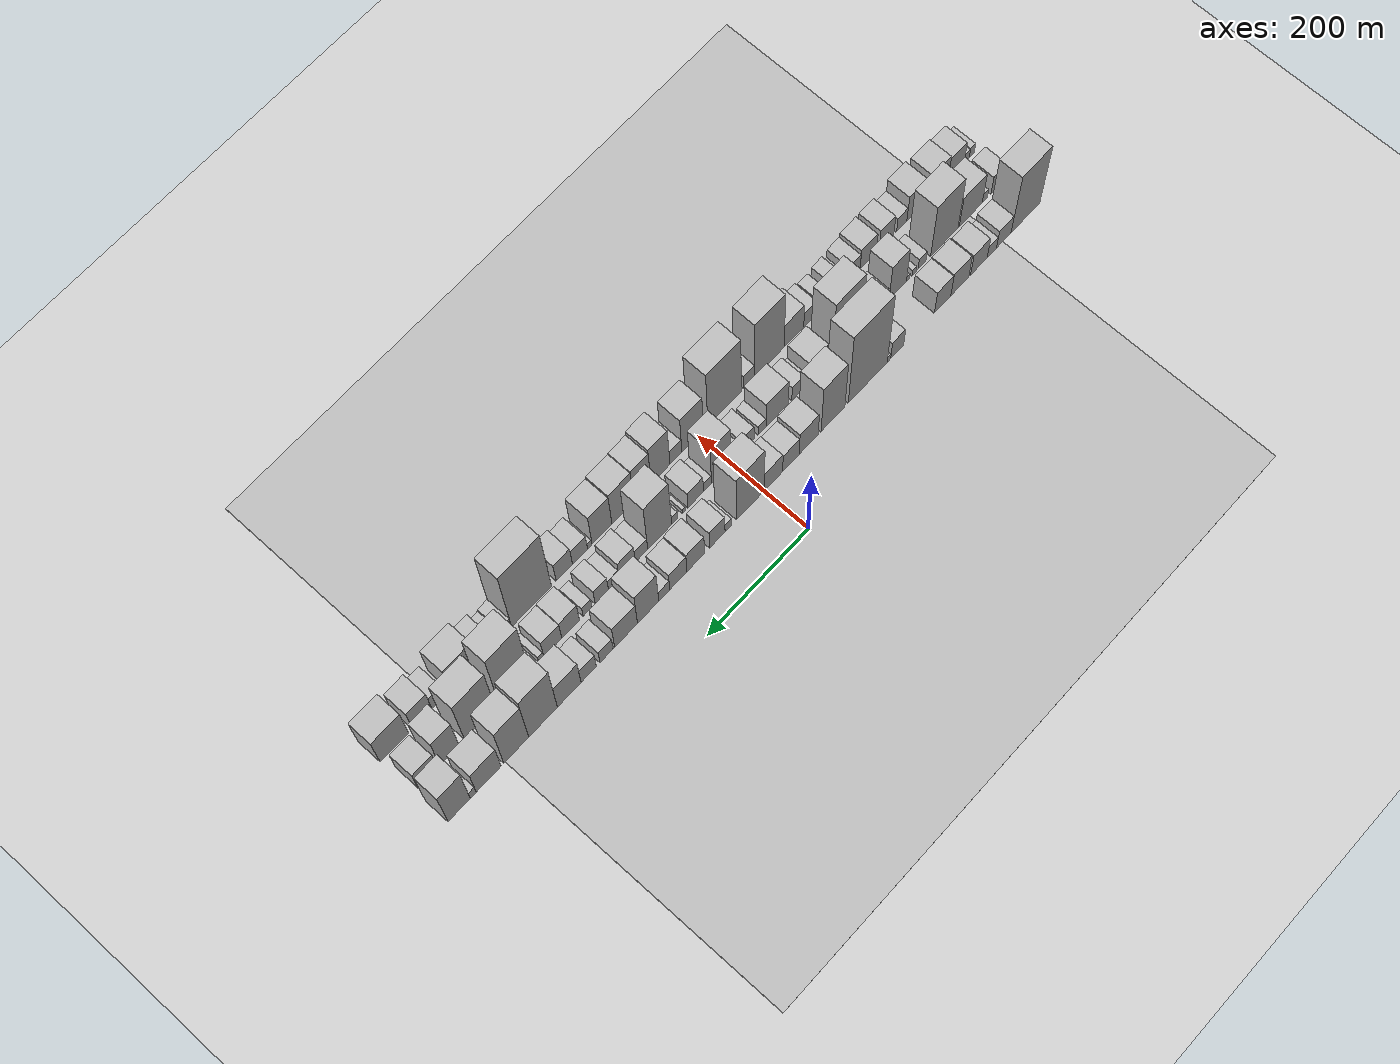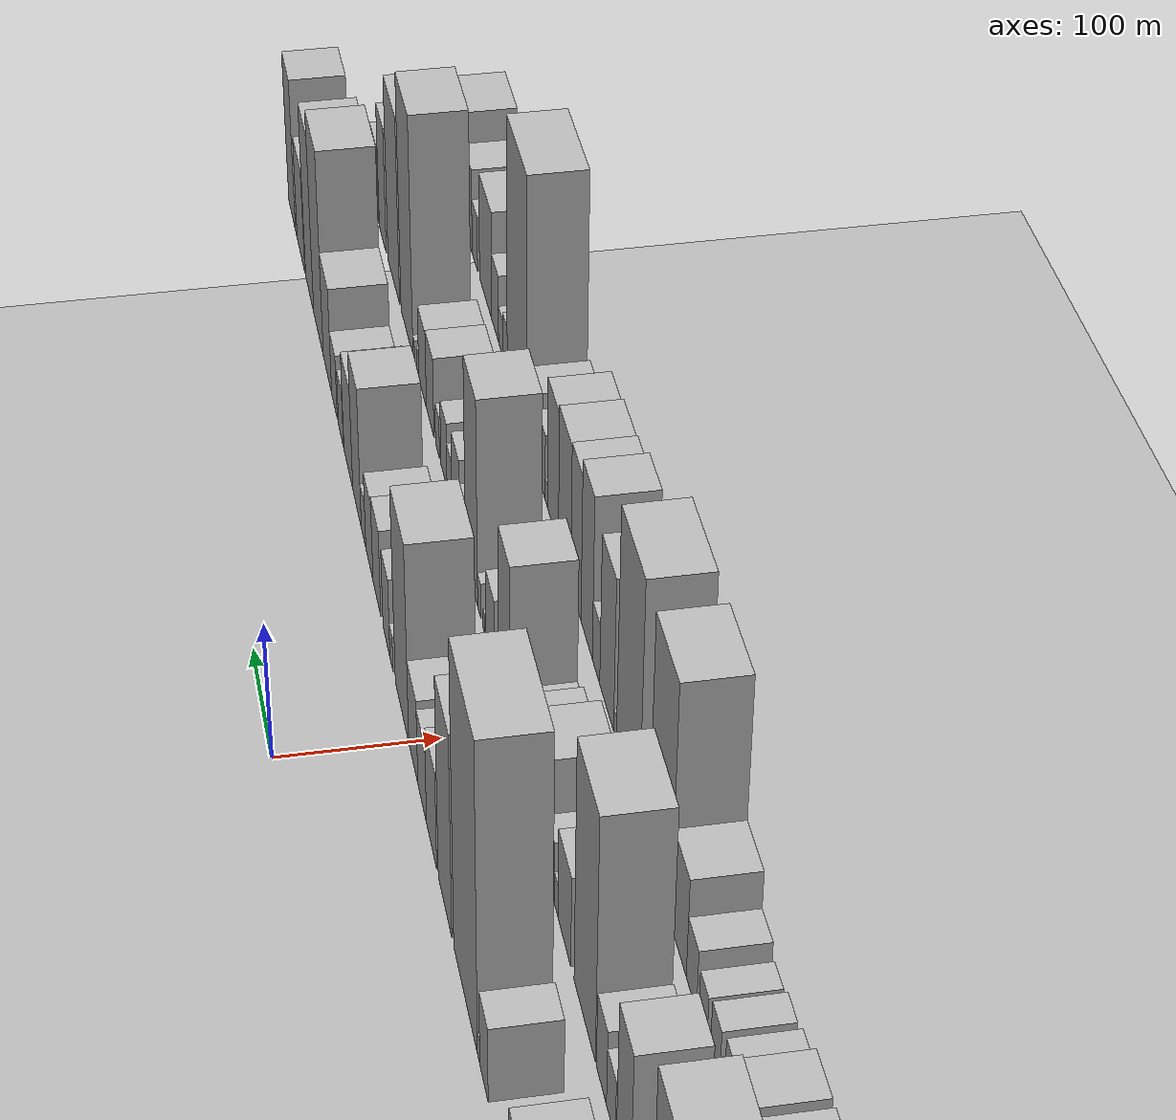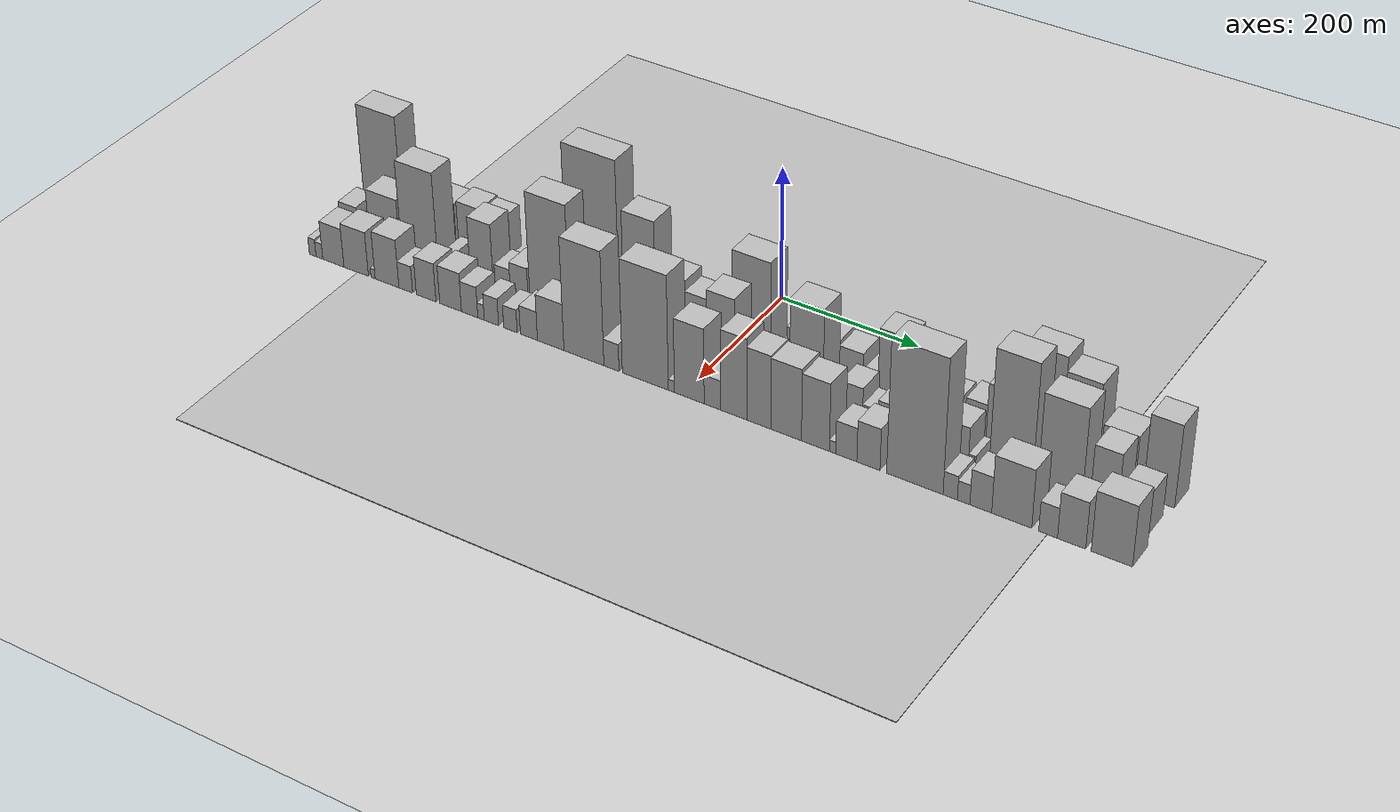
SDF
<?xml version="1.0" encoding="utf-8"?>

<sdf version="1.6">

   <world name="default">

      <gui fullscreen="0">

         <camera name="user_camera">

            <pose>-15 0 4.57585 0 0 0</pose>

            <view_controller>orbit</view_controller>

         </camera>

      </gui>

      <scene>

         <sky>

           <clouds>

             <speed>12</speed>

           </clouds>

         </sky>

         <ambient>0.4 0.4 0.4 1</ambient>

         <background>0.7 0.7 0.7 1</background>

         <shadows>1</shadows>

      </scene>

      <gravity>0 0 -9.8066</gravity>

      <magnetic_field>6e-06 2.3e-05 -4.2e-05</magnetic_field>

      <physics default="0" name="default_physics" type="ode">

         <ode>

            <solver>

               <type>quick</type>

               <iters>10</iters>

               <sor>1.0</sor>

               <use_dynamic_moi_rescaling>0</use_dynamic_moi_rescaling>

            </solver>

            <constraints>

               <cfm>0</cfm>

               <erp>0.2</erp>

               <contact_max_correcting_vel>100</contact_max_correcting_vel>

               <contact_surface_layer>0.001</contact_surface_layer>

            </constraints>

         </ode>

         <max_step_size>0.004</max_step_size>

         <real_time_factor>1</real_time_factor>

         <real_time_update_rate>250</real_time_update_rate>

      </physics>

      <light name="sun" type="directional">

         <cast_shadows>1</cast_shadows>

         <pose>0 0 10 0 0 0</pose>

         <diffuse>0.8 0.8 0.8 1</diffuse>

         <specular>0.2 0.2 0.2 1</specular>

         <attenuation>

            <range>1000</range>

            <constant>0.9</constant>

            <linear>0.01</linear>

            <quadratic>0.001</quadratic>

         </attenuation>

         <direction>-0.5 0.1 -0.9</direction>

      </light>

      <include>

         <name>ground_plane_1</name>

         <uri>model://HANNAS_ground_plane</uri>

         <pose>0 0 0  0 0 0</pose>

      </include>

      <include>

         <name>ground_plane_2</name>

         <uri>model://HANNAS_ground_plane</uri>

         <pose>100 0 0  0 0 0</pose>

      </include>

      <model name="building_1">

         <static>1</static>

         <pose frame="">100.0000 -548.3771 0 0.000000 0.000000 0.000000</pose>

         <link name="link">

            <pose frame="">0 0 84.00 0 0 0</pose>

            <collision name="collision">

               <geometry>

                  <box>

                     <size>40.0000 63.2457 168.0000</size>

                  </box>

               </geometry>

               <max_contacts>10</max_contacts>

               <surface>

                  <contact>

                     <ode/>

                  </contact>

                  <bounce/>

                  <friction>

                     <torsional>

                        <ode/>

                     </torsional>

                     <ode/>

                  </friction>

               </surface>

            </collision>

            <visual name="visual">

               <cast_shadows>0</cast_shadows>

               <geometry>

                  <box>

                     <size>40.0000 63.2457 168.0000</size>

                  </box>

               </geometry>

               <material>

                  <script>

                     <uri>model://HANNAS_wall/materials/scripts</uri>

                     <uri>model://HANNAS_wall/materials/textures</uri>

                     <name>vrc/HANNAS_wall</name>

                  </script>

               </material>

            </visual>

            <self_collide>0</self_collide>

            <enable_wind>0</enable_wind>

            <kinematic>0</kinematic>

         </link>

      </model>

      <model name="building_2">

         <static>1</static>

         <pose frame="">100.0000 -500.9420 0 0.000000 0.000000 0.000000</pose>

         <link name="link">

            <pose frame="">0 0 27.00 0 0 0</pose>

            <collision name="collision">

               <geometry>

                  <box>

                     <size>40.0000 31.6246 54.0000</size>

                  </box>

               </geometry>

               <max_contacts>10</max_contacts>

               <surface>

                  <contact>

                     <ode/>

                  </contact>

                  <bounce/>

                  <friction>

                     <torsional>

                        <ode/>

                     </torsional>

                     <ode/>

                  </friction>

               </surface>

            </collision>

            <visual name="visual">

               <cast_shadows>0</cast_shadows>

               <geometry>

                  <box>

                     <size>40.0000 31.6246 54.0000</size>

                  </box>

               </geometry>

               <material>

                  <script>

                     <uri>model://HANNAS_wall/materials/scripts</uri>

                     <uri>model://HANNAS_wall/materials/textures</uri>

                     <name>vrc/HANNAS_wall</name>

                  </script>

               </material>

            </visual>

            <self_collide>0</self_collide>

            <enable_wind>0</enable_wind>

            <kinematic>0</kinematic>

         </link>

      </model>

      <model name="building_3">

         <static>1</static>

         <pose frame="">100.0000 -475.0238 0 0.000000 0.000000 0.000000</pose>

         <link name="link">

            <pose frame="">0 0 18.00 0 0 0</pose>

            <collision name="collision">

               <geometry>

                  <box>

                     <size>40.0000 20.2117 36.0000</size>

                  </box>

               </geometry>

               <max_contacts>10</max_contacts>

               <surface>

                  <contact>

                     <ode/>

                  </contact>

                  <bounce/>

                  <friction>

                     <torsional>

                        <ode/>

                     </torsional>

                     <ode/>

                  </friction>

               </surface>

            </collision>

            <visual name="visual">

               <cast_shadows>0</cast_shadows>

               <geometry>

                  <box>

                     <size>40.0000 20.2117 36.0000</size>

                  </box>

               </geometry>

               <material>

                  <script>

                     <uri>model://HANNAS_wall/materials/scripts</uri>

                     <uri>model://HANNAS_wall/materials/textures</uri>

                     <name>vrc/HANNAS_wall</name>

                  </script>

               </material>

            </visual>

            <self_collide>0</self_collide>

            <enable_wind>0</enable_wind>

            <kinematic>0</kinematic>

         </link>

      </model>

      <model name="building_4">

         <static>1</static>

         <pose frame="">100.0000 -447.1231 0 0.000000 0.000000 0.000000</pose>

         <link name="link">

            <pose frame="">0 0 31.50 0 0 0</pose>

            <collision name="collision">

               <geometry>

                  <box>

                     <size>40.0000 35.5897 63.0000</size>

                  </box>

               </geometry>

               <max_contacts>10</max_contacts>

               <surface>

                  <contact>

                     <ode/>

                  </contact>

                  <bounce/>

                  <friction>

                     <torsional>

                        <ode/>

                     </torsional>

                     <ode/>

                  </friction>

               </surface>

            </collision>

            <visual name="visual">

               <cast_shadows>0</cast_shadows>

               <geometry>

                  <box>

                     <size>40.0000 35.5897 63.0000</size>

                  </box>

               </geometry>

               <material>

                  <script>

                     <uri>model://HANNAS_wall/materials/scripts</uri>

                     <uri>model://HANNAS_wall/materials/textures</uri>

                     <name>vrc/HANNAS_wall</name>

                  </script>

               </material>

            </visual>

            <self_collide>0</self_collide>

            <enable_wind>0</enable_wind>

            <kinematic>0</kinematic>

         </link>

      </model>

      <model name="building_5">

         <static>1</static>

         <pose frame="">100.0000 -406.2347 0 0.000000 0.000000 0.000000</pose>

         <link name="link">

            <pose frame="">0 0 34.50 0 0 0</pose>

            <collision name="collision">

               <geometry>

                  <box>

                     <size>40.0000 38.1872 69.0000</size>

                  </box>

               </geometry>

               <max_contacts>10</max_contacts>

               <surface>

                  <contact>

                     <ode/>

                  </contact>

                  <bounce/>

                  <friction>

                     <torsional>

                        <ode/>

                     </torsional>

                     <ode/>

                  </friction>

               </surface>

            </collision>

            <visual name="visual">

               <cast_shadows>0</cast_shadows>

               <geometry>

                  <box>

                     <size>40.0000 38.1872 69.0000</size>

                  </box>

               </geometry>

               <material>

                  <script>

                     <uri>model://HANNAS_wall/materials/scripts</uri>

                     <uri>model://HANNAS_wall/materials/textures</uri>

                     <name>vrc/HANNAS_wall</name>

                  </script>

               </material>

            </visual>

            <self_collide>0</self_collide>

            <enable_wind>0</enable_wind>

            <kinematic>0</kinematic>

         </link>

      </model>

      <model name="building_6">

         <static>1</static>

         <pose frame="">100.0000 -369.8008 0 0.000000 0.000000 0.000000</pose>

         <link name="link">

            <pose frame="">0 0 33.00 0 0 0</pose>

            <collision name="collision">

               <geometry>

                  <box>

                     <size>40.0000 34.6807 66.0000</size>

                  </box>

               </geometry>

               <max_contacts>10</max_contacts>

               <surface>

                  <contact>

                     <ode/>

                  </contact>

                  <bounce/>

                  <friction>

                     <torsional>

                        <ode/>

                     </torsional>

                     <ode/>

                  </friction>

               </surface>

            </collision>

            <visual name="visual">

               <cast_shadows>0</cast_shadows>

               <geometry>

                  <box>

                     <size>40.0000 34.6807 66.0000</size>

                  </box>

               </geometry>

               <material>

                  <script>

                     <uri>model://HANNAS_wall/materials/scripts</uri>

                     <uri>model://HANNAS_wall/materials/textures</uri>

                     <name>vrc/HANNAS_wall</name>

                  </script>

               </material>

            </visual>

            <self_collide>0</self_collide>

            <enable_wind>0</enable_wind>

            <kinematic>0</kinematic>

         </link>

      </model>

      <model name="building_7">

         <static>1</static>

         <pose frame="">100.0000 -273.6054 0 0.000000 0.000000 0.000000</pose>

         <link name="link">

            <pose frame="">0 0 27.00 0 0 0</pose>

            <collision name="collision">

               <geometry>

                  <box>

                     <size>40.0000 27.2367 54.0000</size>

                  </box>

               </geometry>

               <max_contacts>10</max_contacts>

               <surface>

                  <contact>

                     <ode/>

                  </contact>

                  <bounce/>

                  <friction>

                     <torsional>

                        <ode/>

                     </torsional>

                     <ode/>

                  </friction>

               </surface>

            </collision>

            <visual name="visual">

               <cast_shadows>0</cast_shadows>

               <geometry>

                  <box>

                     <size>40.0000 27.2367 54.0000</size>

                  </box>

               </geometry>

               <material>

                  <script>

                     <uri>model://HANNAS_wall/materials/scripts</uri>

                     <uri>model://HANNAS_wall/materials/textures</uri>

                     <name>vrc/HANNAS_wall</name>

                  </script>

               </material>

            </visual>

            <self_collide>0</self_collide>

            <enable_wind>0</enable_wind>

            <kinematic>0</kinematic>

         </link>

      </model>

      <model name="building_8">

         <static>1</static>

         <pose frame="">100.0000 -256.3107 0 0.000000 0.000000 0.000000</pose>

         <link name="link">

            <pose frame="">0 0 9.00 0 0 0</pose>

            <collision name="collision">

               <geometry>

                  <box>

                     <size>40.0000 7.3528 18.0000</size>

                  </box>

               </geometry>

               <max_contacts>10</max_contacts>

               <surface>

                  <contact>

                     <ode/>

                  </contact>

                  <bounce/>

                  <friction>

                     <torsional>

                        <ode/>

                     </torsional>

                     <ode/>

                  </friction>

               </surface>

            </collision>

            <visual name="visual">

               <cast_shadows>0</cast_shadows>

               <geometry>

                  <box>

                     <size>40.0000 7.3528 18.0000</size>

                  </box>

               </geometry>

               <material>

                  <script>

                     <uri>model://HANNAS_wall/materials/scripts</uri>

                     <uri>model://HANNAS_wall/materials/textures</uri>

                     <name>vrc/HANNAS_wall</name>

                  </script>

               </material>

            </visual>

            <self_collide>0</self_collide>

            <enable_wind>0</enable_wind>

            <kinematic>0</kinematic>

         </link>

      </model>

      <model name="building_9">

         <static>1</static>

         <pose frame="">100.0000 -212.1826 0 0.000000 0.000000 0.000000</pose>

         <link name="link">

            <pose frame="">0 0 109.50 0 0 0</pose>

            <collision name="collision">

               <geometry>

                  <box>

                     <size>40.0000 80.9033 219.0000</size>

                  </box>

               </geometry>

               <max_contacts>10</max_contacts>

               <surface>

                  <contact>

                     <ode/>

                  </contact>

                  <bounce/>

                  <friction>

                     <torsional>

                        <ode/>

                     </torsional>

                     <ode/>

                  </friction>

               </surface>

            </collision>

            <visual name="visual">

               <cast_shadows>0</cast_shadows>

               <geometry>

                  <box>

                     <size>40.0000 80.9033 219.0000</size>

                  </box>

               </geometry>

               <material>

                  <script>

                     <uri>model://HANNAS_wall/materials/scripts</uri>

                     <uri>model://HANNAS_wall/materials/textures</uri>

                     <name>vrc/HANNAS_wall</name>

                  </script>

               </material>

            </visual>

            <self_collide>0</self_collide>

            <enable_wind>0</enable_wind>

            <kinematic>0</kinematic>

         </link>

      </model>

      <model name="building_10">

         <static>1</static>

         <pose frame="">100.0000 -140.3099 0 0.000000 0.000000 0.000000</pose>

         <link name="link">

            <pose frame="">0 0 73.50 0 0 0</pose>

            <collision name="collision">

               <geometry>

                  <box>

                     <size>40.0000 48.8421 147.0000</size>

                  </box>

               </geometry>

               <max_contacts>10</max_contacts>

               <surface>

                  <contact>

                     <ode/>

                  </contact>

                  <bounce/>

                  <friction>

                     <torsional>

                        <ode/>

                     </torsional>

                     <ode/>

                  </friction>

               </surface>

            </collision>

            <visual name="visual">

               <cast_shadows>0</cast_shadows>

               <geometry>

                  <box>

                     <size>40.0000 48.8421 147.0000</size>

                  </box>

               </geometry>

               <material>

                  <script>

                     <uri>model://HANNAS_wall/materials/scripts</uri>

                     <uri>model://HANNAS_wall/materials/textures</uri>

                     <name>vrc/HANNAS_wall</name>

                  </script>

               </material>

            </visual>

            <self_collide>0</self_collide>

            <enable_wind>0</enable_wind>

            <kinematic>0</kinematic>

         </link>

      </model>

      <model name="building_11">

         <static>1</static>

         <pose frame="">100.0000 -90.5646 0 0.000000 0.000000 0.000000</pose>

         <link name="link">

            <pose frame="">0 0 36.00 0 0 0</pose>

            <collision name="collision">

               <geometry>

                  <box>

                     <size>40.0000 38.6485 72.0000</size>

                  </box>

               </geometry>

               <max_contacts>10</max_contacts>

               <surface>

                  <contact>

                     <ode/>

                  </contact>

                  <bounce/>

                  <friction>

                     <torsional>

                        <ode/>

                     </torsional>

                     <ode/>

                  </friction>

               </surface>

            </collision>

            <visual name="visual">

               <cast_shadows>0</cast_shadows>

               <geometry>

                  <box>

                     <size>40.0000 38.6485 72.0000</size>

                  </box>

               </geometry>

               <material>

                  <script>

                     <uri>model://HANNAS_wall/materials/scripts</uri>

                     <uri>model://HANNAS_wall/materials/textures</uri>

                     <name>vrc/HANNAS_wall</name>

                  </script>

               </material>

            </visual>

            <self_collide>0</self_collide>

            <enable_wind>0</enable_wind>

            <kinematic>0</kinematic>

         </link>

      </model>

      <model name="building_12">

         <static>1</static>

         <pose frame="">100.0000 -54.4767 0 0.000000 0.000000 0.000000</pose>

         <link name="link">

            <pose frame="">0 0 28.50 0 0 0</pose>

            <collision name="collision">

               <geometry>

                  <box>

                     <size>40.0000 33.5274 57.0000</size>

                  </box>

               </geometry>

               <max_contacts>10</max_contacts>

               <surface>

                  <contact>

                     <ode/>

                  </contact>

                  <bounce/>

                  <friction>

                     <torsional>

                        <ode/>

                     </torsional>

                     <ode/>

                  </friction>

               </surface>

            </collision>

            <visual name="visual">

               <cast_shadows>0</cast_shadows>

               <geometry>

                  <box>

                     <size>40.0000 33.5274 57.0000</size>

                  </box>

               </geometry>

               <material>

                  <script>

                     <uri>model://HANNAS_wall/materials/scripts</uri>

                     <uri>model://HANNAS_wall/materials/textures</uri>

                     <name>vrc/HANNAS_wall</name>

                  </script>

               </material>

            </visual>

            <self_collide>0</self_collide>

            <enable_wind>0</enable_wind>

            <kinematic>0</kinematic>

         </link>

      </model>

      <model name="building_13">

         <static>1</static>

         <pose frame="">100.0000 -19.4294 0 0.000000 0.000000 0.000000</pose>

         <link name="link">

            <pose frame="">0 0 31.50 0 0 0</pose>

            <collision name="collision">

               <geometry>

                  <box>

                     <size>40.0000 36.5672 63.0000</size>

                  </box>

               </geometry>

               <max_contacts>10</max_contacts>

               <surface>

                  <contact>

                     <ode/>

                  </contact>

                  <bounce/>

                  <friction>

                     <torsional>

                        <ode/>

                     </torsional>

                     <ode/>

                  </friction>

               </surface>

            </collision>

            <visual name="visual">

               <cast_shadows>0</cast_shadows>

               <geometry>

                  <box>

                     <size>40.0000 36.5672 63.0000</size>

                  </box>

               </geometry>

               <material>

                  <script>

                     <uri>model://HANNAS_wall/materials/scripts</uri>

                     <uri>model://HANNAS_wall/materials/textures</uri>

                     <name>vrc/HANNAS_wall</name>

                  </script>

               </material>

            </visual>

            <self_collide>0</self_collide>

            <enable_wind>0</enable_wind>

            <kinematic>0</kinematic>

         </link>

      </model>

      <model name="building_14">

         <static>1</static>

         <pose frame="">100.0000 26.7737 0 0.000000 0.000000 0.000000</pose>

         <link name="link">

            <pose frame="">0 0 73.50 0 0 0</pose>

            <collision name="collision">

               <geometry>

                  <box>

                     <size>40.0000 55.8390 147.0000</size>

                  </box>

               </geometry>

               <max_contacts>10</max_contacts>

               <surface>

                  <contact>

                     <ode/>

                  </contact>

                  <bounce/>

                  <friction>

                     <torsional>

                        <ode/>

                     </torsional>

                     <ode/>

                  </friction>

               </surface>

            </collision>

            <visual name="visual">

               <cast_shadows>0</cast_shadows>

               <geometry>

                  <box>

                     <size>40.0000 55.8390 147.0000</size>

                  </box>

               </geometry>

               <material>

                  <script>

                     <uri>model://HANNAS_wall/materials/scripts</uri>

                     <uri>model://HANNAS_wall/materials/textures</uri>

                     <name>vrc/HANNAS_wall</name>

                  </script>

               </material>

            </visual>

            <self_collide>0</self_collide>

            <enable_wind>0</enable_wind>

            <kinematic>0</kinematic>

         </link>

      </model>

      <model name="building_15">

         <static>1</static>

         <pose frame="">100.0000 71.2728 0 0.000000 0.000000 0.000000</pose>

         <link name="link">

            <pose frame="">0 0 13.50 0 0 0</pose>

            <collision name="collision">

               <geometry>

                  <box>

                     <size>40.0000 13.1591 27.0000</size>

                  </box>

               </geometry>

               <max_contacts>10</max_contacts>

               <surface>

                  <contact>

                     <ode/>

                  </contact>

                  <bounce/>

                  <friction>

                     <torsional>

                        <ode/>

                     </torsional>

                     <ode/>

                  </friction>

               </surface>

            </collision>

            <visual name="visual">

               <cast_shadows>0</cast_shadows>

               <geometry>

                  <box>

                     <size>40.0000 13.1591 27.0000</size>

                  </box>

               </geometry>

               <material>

                  <script>

                     <uri>model://HANNAS_wall/materials/scripts</uri>

                     <uri>model://HANNAS_wall/materials/textures</uri>

                     <name>vrc/HANNAS_wall</name>

                  </script>

               </material>

            </visual>

            <self_collide>0</self_collide>

            <enable_wind>0</enable_wind>

            <kinematic>0</kinematic>

         </link>

      </model>

      <model name="building_16">

         <static>1</static>

         <pose frame="">100.0000 93.0331 0 0.000000 0.000000 0.000000</pose>

         <link name="link">

            <pose frame="">0 0 30.00 0 0 0</pose>

            <collision name="collision">

               <geometry>

                  <box>

                     <size>40.0000 30.3615 60.0000</size>

                  </box>

               </geometry>

               <max_contacts>10</max_contacts>

               <surface>

                  <contact>

                     <ode/>

                  </contact>

                  <bounce/>

                  <friction>

                     <torsional>

                        <ode/>

                     </torsional>

                     <ode/>

                  </friction>

               </surface>

            </collision>

            <visual name="visual">

               <cast_shadows>0</cast_shadows>

               <geometry>

                  <box>

                     <size>40.0000 30.3615 60.0000</size>

                  </box>

               </geometry>

               <material>

                  <script>

                     <uri>model://HANNAS_wall/materials/scripts</uri>

                     <uri>model://HANNAS_wall/materials/textures</uri>

                     <name>vrc/HANNAS_wall</name>

                  </script>

               </material>

            </visual>

            <self_collide>0</self_collide>

            <enable_wind>0</enable_wind>

            <kinematic>0</kinematic>

         </link>

      </model>

      <model name="building_17">

         <static>1</static>

         <pose frame="">100.0000 135.6121 0 0.000000 0.000000 0.000000</pose>

         <link name="link">

            <pose frame="">0 0 33.00 0 0 0</pose>

            <collision name="collision">

               <geometry>

                  <box>

                     <size>40.0000 34.7966 66.0000</size>

                  </box>

               </geometry>

               <max_contacts>10</max_contacts>

               <surface>

                  <contact>

                     <ode/>

                  </contact>

                  <bounce/>

                  <friction>

                     <torsional>

                        <ode/>

                     </torsional>

                     <ode/>

                  </friction>

               </surface>

            </collision>

            <visual name="visual">

               <cast_shadows>0</cast_shadows>

               <geometry>

                  <box>

                     <size>40.0000 34.7966 66.0000</size>

                  </box>

               </geometry>

               <material>

                  <script>

                     <uri>model://HANNAS_wall/materials/scripts</uri>

                     <uri>model://HANNAS_wall/materials/textures</uri>

                     <name>vrc/HANNAS_wall</name>

                  </script>

               </material>

            </visual>

            <self_collide>0</self_collide>

            <enable_wind>0</enable_wind>

            <kinematic>0</kinematic>

         </link>

      </model>

      <model name="building_18">

         <static>1</static>

         <pose frame="">100.0000 169.8509 0 0.000000 0.000000 0.000000</pose>

         <link name="link">

            <pose frame="">0 0 30.00 0 0 0</pose>

            <collision name="collision">

               <geometry>

                  <box>

                     <size>40.0000 33.6808 60.0000</size>

                  </box>

               </geometry>

               <max_contacts>10</max_contacts>

               <surface>

                  <contact>

                     <ode/>

                  </contact>

                  <bounce/>

                  <friction>

                     <torsional>

                        <ode/>

                     </torsional>

                     <ode/>

                  </friction>

               </surface>

            </collision>

            <visual name="visual">

               <cast_shadows>0</cast_shadows>

               <geometry>

                  <box>

                     <size>40.0000 33.6808 60.0000</size>

                  </box>

               </geometry>

               <material>

                  <script>

                     <uri>model://HANNAS_wall/materials/scripts</uri>

                     <uri>model://HANNAS_wall/materials/textures</uri>

                     <name>vrc/HANNAS_wall</name>

                  </script>

               </material>

            </visual>

            <self_collide>0</self_collide>

            <enable_wind>0</enable_wind>

            <kinematic>0</kinematic>

         </link>

      </model>

      <model name="building_19">

         <static>1</static>

         <pose frame="">100.0000 197.3704 0 0.000000 0.000000 0.000000</pose>

         <link name="link">

            <pose frame="">0 0 18.00 0 0 0</pose>

            <collision name="collision">

               <geometry>

                  <box>

                     <size>40.0000 21.3583 36.0000</size>

                  </box>

               </geometry>

               <max_contacts>10</max_contacts>

               <surface>

                  <contact>

                     <ode/>

                  </contact>

                  <bounce/>

                  <friction>

                     <torsional>

                        <ode/>

                     </torsional>

                     <ode/>

                  </friction>

               </surface>

            </collision>

            <visual name="visual">

               <cast_shadows>0</cast_shadows>

               <geometry>

                  <box>

                     <size>40.0000 21.3583 36.0000</size>

                  </box>

               </geometry>

               <material>

                  <script>

                     <uri>model://HANNAS_wall/materials/scripts</uri>

                     <uri>model://HANNAS_wall/materials/textures</uri>

                     <name>vrc/HANNAS_wall</name>

                  </script>

               </material>

            </visual>

            <self_collide>0</self_collide>

            <enable_wind>0</enable_wind>

            <kinematic>0</kinematic>

         </link>

      </model>

      <model name="building_20">

         <static>1</static>

         <pose frame="">100.0000 228.7402 0 0.000000 0.000000 0.000000</pose>

         <link name="link">

            <pose frame="">0 0 54.00 0 0 0</pose>

            <collision name="collision">

               <geometry>

                  <box>

                     <size>40.0000 41.3813 108.0000</size>

                  </box>

               </geometry>

               <max_contacts>10</max_contacts>

               <surface>

                  <contact>

                     <ode/>

                  </contact>

                  <bounce/>

                  <friction>

                     <torsional>

                        <ode/>

                     </torsional>

                     <ode/>

                  </friction>

               </surface>

            </collision>

            <visual name="visual">

               <cast_shadows>0</cast_shadows>

               <geometry>

                  <box>

                     <size>40.0000 41.3813 108.0000</size>

                  </box>

               </geometry>

               <material>

                  <script>

                     <uri>model://HANNAS_wall/materials/scripts</uri>

                     <uri>model://HANNAS_wall/materials/textures</uri>

                     <name>vrc/HANNAS_wall</name>

                  </script>

               </material>

            </visual>

            <self_collide>0</self_collide>

            <enable_wind>0</enable_wind>

            <kinematic>0</kinematic>

         </link>

      </model>

      <model name="building_21">

         <static>1</static>

         <pose frame="">100.0000 271.4339 0 0.000000 0.000000 0.000000</pose>

         <link name="link">

            <pose frame="">0 0 39.00 0 0 0</pose>

            <collision name="collision">

               <geometry>

                  <box>

                     <size>40.0000 44.0061 78.0000</size>

                  </box>

               </geometry>

               <max_contacts>10</max_contacts>

               <surface>

                  <contact>

                     <ode/>

                  </contact>

                  <bounce/>

                  <friction>

                     <torsional>

                        <ode/>

                     </torsional>

                     <ode/>

                  </friction>

               </surface>

            </collision>

            <visual name="visual">

               <cast_shadows>0</cast_shadows>

               <geometry>

                  <box>

                     <size>40.0000 44.0061 78.0000</size>

                  </box>

               </geometry>

               <material>

                  <script>

                     <uri>model://HANNAS_wall/materials/scripts</uri>

                     <uri>model://HANNAS_wall/materials/textures</uri>

                     <name>vrc/HANNAS_wall</name>

                  </script>

               </material>

            </visual>

            <self_collide>0</self_collide>

            <enable_wind>0</enable_wind>

            <kinematic>0</kinematic>

         </link>

      </model>

      <model name="building_22">

         <static>1</static>

         <pose frame="">100.0000 308.9421 0 0.000000 0.000000 0.000000</pose>

         <link name="link">

            <pose frame="">0 0 22.50 0 0 0</pose>

            <collision name="collision">

               <geometry>

                  <box>

                     <size>40.0000 25.0101 45.0000</size>

                  </box>

               </geometry>

               <max_contacts>10</max_contacts>

               <surface>

                  <contact>

                     <ode/>

                  </contact>

                  <bounce/>

                  <friction>

                     <torsional>

                        <ode/>

                     </torsional>

                     <ode/>

                  </friction>

               </surface>

            </collision>

            <visual name="visual">

               <cast_shadows>0</cast_shadows>

               <geometry>

                  <box>

                     <size>40.0000 25.0101 45.0000</size>

                  </box>

               </geometry>

               <material>

                  <script>

                     <uri>model://HANNAS_wall/materials/scripts</uri>

                     <uri>model://HANNAS_wall/materials/textures</uri>

                     <name>vrc/HANNAS_wall</name>

                  </script>

               </material>

            </visual>

            <self_collide>0</self_collide>

            <enable_wind>0</enable_wind>

            <kinematic>0</kinematic>

         </link>

      </model>

      <model name="building_23">

         <static>1</static>

         <pose frame="">100.0000 343.0104 0 0.000000 0.000000 0.000000</pose>

         <link name="link">

            <pose frame="">0 0 25.50 0 0 0</pose>

            <collision name="collision">

               <geometry>

                  <box>

                     <size>40.0000 29.1266 51.0000</size>

                  </box>

               </geometry>

               <max_contacts>10</max_contacts>

               <surface>

                  <contact>

                     <ode/>

                  </contact>

                  <bounce/>

                  <friction>

                     <torsional>

                        <ode/>

                     </torsional>

                     <ode/>

                  </friction>

               </surface>

            </collision>

            <visual name="visual">

               <cast_shadows>0</cast_shadows>

               <geometry>

                  <box>

                     <size>40.0000 29.1266 51.0000</size>

                  </box>

               </geometry>

               <material>

                  <script>

                     <uri>model://HANNAS_wall/materials/scripts</uri>

                     <uri>model://HANNAS_wall/materials/textures</uri>

                     <name>vrc/HANNAS_wall</name>

                  </script>

               </material>

            </visual>

            <self_collide>0</self_collide>

            <enable_wind>0</enable_wind>

            <kinematic>0</kinematic>

         </link>

      </model>

      <model name="building_24">

         <static>1</static>

         <pose frame="">100.0000 380.0069 0 0.000000 0.000000 0.000000</pose>

         <link name="link">

            <pose frame="">0 0 42.00 0 0 0</pose>

            <collision name="collision">

               <geometry>

                  <box>

                     <size>40.0000 44.8663 84.0000</size>

                  </box>

               </geometry>

               <max_contacts>10</max_contacts>

               <surface>

                  <contact>

                     <ode/>

                  </contact>

                  <bounce/>

                  <friction>

                     <torsional>

                        <ode/>

                     </torsional>

                     <ode/>

                  </friction>

               </surface>

            </collision>

            <visual name="visual">

               <cast_shadows>0</cast_shadows>

               <geometry>

                  <box>

                     <size>40.0000 44.8663 84.0000</size>

                  </box>

               </geometry>

               <material>

                  <script>

                     <uri>model://HANNAS_wall/materials/scripts</uri>

                     <uri>model://HANNAS_wall/materials/textures</uri>

                     <name>vrc/HANNAS_wall</name>

                  </script>

               </material>

            </visual>

            <self_collide>0</self_collide>

            <enable_wind>0</enable_wind>

            <kinematic>0</kinematic>

         </link>

      </model>

      <model name="building_25">

         <static>1</static>

         <pose frame="">100.0000 429.3852 0 0.000000 0.000000 0.000000</pose>

         <link name="link">

            <pose frame="">0 0 81.00 0 0 0</pose>

            <collision name="collision">

               <geometry>

                  <box>

                     <size>40.0000 53.8903 162.0000</size>

                  </box>

               </geometry>

               <max_contacts>10</max_contacts>

               <surface>

                  <contact>

                     <ode/>

                  </contact>

                  <bounce/>

                  <friction>

                     <torsional>

                        <ode/>

                     </torsional>

                     <ode/>

                  </friction>

               </surface>

            </collision>

            <visual name="visual">

               <cast_shadows>0</cast_shadows>

               <geometry>

                  <box>

                     <size>40.0000 53.8903 162.0000</size>

                  </box>

               </geometry>

               <material>

                  <script>

                     <uri>model://HANNAS_wall/materials/scripts</uri>

                     <uri>model://HANNAS_wall/materials/textures</uri>

                     <name>vrc/HANNAS_wall</name>

                  </script>

               </material>

            </visual>

            <self_collide>0</self_collide>

            <enable_wind>0</enable_wind>

            <kinematic>0</kinematic>

         </link>

      </model>

      <model name="building_26">

         <static>1</static>

         <pose frame="">100.0000 479.6066 0 0.000000 0.000000 0.000000</pose>

         <link name="link">

            <pose frame="">0 0 70.50 0 0 0</pose>

            <collision name="collision">

               <geometry>

                  <box>

                     <size>40.0000 46.5524 141.0000</size>

                  </box>

               </geometry>

               <max_contacts>10</max_contacts>

               <surface>

                  <contact>

                     <ode/>

                  </contact>

                  <bounce/>

                  <friction>

                     <torsional>

                        <ode/>

                     </torsional>

                     <ode/>

                  </friction>

               </surface>

            </collision>

            <visual name="visual">

               <cast_shadows>0</cast_shadows>

               <geometry>

                  <box>

                     <size>40.0000 46.5524 141.0000</size>

                  </box>

               </geometry>

               <material>

                  <script>

                     <uri>model://HANNAS_wall/materials/scripts</uri>

                     <uri>model://HANNAS_wall/materials/textures</uri>

                     <name>vrc/HANNAS_wall</name>

                  </script>

               </material>

            </visual>

            <self_collide>0</self_collide>

            <enable_wind>0</enable_wind>

            <kinematic>0</kinematic>

         </link>

      </model>

      <model name="building_27">

         <static>1</static>

         <pose frame="">100.0000 530.8130 0 0.000000 0.000000 0.000000</pose>

         <link name="link">

            <pose frame="">0 0 42.00 0 0 0</pose>

            <collision name="collision">

               <geometry>

                  <box>

                     <size>40.0000 45.8605 84.0000</size>

                  </box>

               </geometry>

               <max_contacts>10</max_contacts>

               <surface>

                  <contact>

                     <ode/>

                  </contact>

                  <bounce/>

                  <friction>

                     <torsional>

                        <ode/>

                     </torsional>

                     <ode/>

                  </friction>

               </surface>

            </collision>

            <visual name="visual">

               <cast_shadows>0</cast_shadows>

               <geometry>

                  <box>

                     <size>40.0000 45.8605 84.0000</size>

                  </box>

               </geometry>

               <material>

                  <script>

                     <uri>model://HANNAS_wall/materials/scripts</uri>

                     <uri>model://HANNAS_wall/materials/textures</uri>

                     <name>vrc/HANNAS_wall</name>

                  </script>

               </material>

            </visual>

            <self_collide>0</self_collide>

            <enable_wind>0</enable_wind>

            <kinematic>0</kinematic>

         </link>

      </model>

      <model name="building_28">

         <static>1</static>

         <pose frame="">100.0000 559.2365 0 0.000000 0.000000 0.000000</pose>

         <link name="link">

            <pose frame="">0 0 13.50 0 0 0</pose>

            <collision name="collision">

               <geometry>

                  <box>

                     <size>40.0000 10.9863 27.0000</size>

                  </box>

               </geometry>

               <max_contacts>10</max_contacts>

               <surface>

                  <contact>

                     <ode/>

                  </contact>

                  <bounce/>

                  <friction>

                     <torsional>

                        <ode/>

                     </torsional>

                     <ode/>

                  </friction>

               </surface>

            </collision>

            <visual name="visual">

               <cast_shadows>0</cast_shadows>

               <geometry>

                  <box>

                     <size>40.0000 10.9863 27.0000</size>

                  </box>

               </geometry>

               <material>

                  <script>

                     <uri>model://HANNAS_wall/materials/scripts</uri>

                     <uri>model://HANNAS_wall/materials/textures</uri>

                     <name>vrc/HANNAS_wall</name>

                  </script>

               </material>

            </visual>

            <self_collide>0</self_collide>

            <enable_wind>0</enable_wind>

            <kinematic>0</kinematic>

         </link>

      </model>

      <model name="building_29">

         <static>1</static>

         <pose frame="">100.0000 585.1890 0 0.000000 0.000000 0.000000</pose>

         <link name="link">

            <pose frame="">0 0 61.50 0 0 0</pose>

            <collision name="collision">

               <geometry>

                  <box>

                     <size>40.0000 40.9187 123.0000</size>

                  </box>

               </geometry>

               <max_contacts>10</max_contacts>

               <surface>

                  <contact>

                     <ode/>

                  </contact>

                  <bounce/>

                  <friction>

                     <torsional>

                        <ode/>

                     </torsional>

                     <ode/>

                  </friction>

               </surface>

            </collision>

            <visual name="visual">

               <cast_shadows>0</cast_shadows>

               <geometry>

                  <box>

                     <size>40.0000 40.9187 123.0000</size>

                  </box>

               </geometry>

               <material>

                  <script>

                     <uri>model://HANNAS_wall/materials/scripts</uri>

                     <uri>model://HANNAS_wall/materials/textures</uri>

                     <name>vrc/HANNAS_wall</name>

                  </script>

               </material>

            </visual>

            <self_collide>0</self_collide>

            <enable_wind>0</enable_wind>

            <kinematic>0</kinematic>

         </link>

      </model>

      <model name="building_30">

         <static>1</static>

         <pose frame="">160.0000 -559.5508 0 0.000000 0.000000 0.000000</pose>

         <link name="link">

            <pose frame="">0 0 25.50 0 0 0</pose>

            <collision name="collision">

               <geometry>

                  <box>

                     <size>40.0000 28.8984 51.0000</size>

                  </box>

               </geometry>

               <max_contacts>10</max_contacts>

               <surface>

                  <contact>

                     <ode/>

                  </contact>

                  <bounce/>

                  <friction>

                     <torsional>

                        <ode/>

                     </torsional>

                     <ode/>

                  </friction>

               </surface>

            </collision>

            <visual name="visual">

               <cast_shadows>0</cast_shadows>

               <geometry>

                  <box>

                     <size>40.0000 28.8984 51.0000</size>

                  </box>

               </geometry>

               <material>

                  <script>

                     <uri>model://HANNAS_wall/materials/scripts</uri>

                     <uri>model://HANNAS_wall/materials/textures</uri>

                     <name>vrc/HANNAS_wall</name>

                  </script>

               </material>

            </visual>

            <self_collide>0</self_collide>

            <enable_wind>0</enable_wind>

            <kinematic>0</kinematic>

         </link>

      </model>

      <model name="building_31">

         <static>1</static>

         <pose frame="">160.0000 -531.5148 0 0.000000 0.000000 0.000000</pose>

         <link name="link">

            <pose frame="">0 0 13.50 0 0 0</pose>

            <collision name="collision">

               <geometry>

                  <box>

                     <size>40.0000 11.1736 27.0000</size>

                  </box>

               </geometry>

               <max_contacts>10</max_contacts>

               <surface>

                  <contact>

                     <ode/>

                  </contact>

                  <bounce/>

                  <friction>

                     <torsional>

                        <ode/>

                     </torsional>

                     <ode/>

                  </friction>

               </surface>

            </collision>

            <visual name="visual">

               <cast_shadows>0</cast_shadows>

               <geometry>

                  <box>

                     <size>40.0000 11.1736 27.0000</size>

                  </box>

               </geometry>

               <material>

                  <script>

                     <uri>model://HANNAS_wall/materials/scripts</uri>

                     <uri>model://HANNAS_wall/materials/textures</uri>

                     <name>vrc/HANNAS_wall</name>

                  </script>

               </material>

            </visual>

            <self_collide>0</self_collide>

            <enable_wind>0</enable_wind>

            <kinematic>0</kinematic>

         </link>

      </model>

      <model name="building_32">

         <static>1</static>

         <pose frame="">160.0000 -500.9850 0 0.000000 0.000000 0.000000</pose>

         <link name="link">

            <pose frame="">0 0 43.50 0 0 0</pose>

            <collision name="collision">

               <geometry>

                  <box>

                     <size>40.0000 49.8860 87.0000</size>

                  </box>

               </geometry>

               <max_contacts>10</max_contacts>

               <surface>

                  <contact>

                     <ode/>

                  </contact>

                  <bounce/>

                  <friction>

                     <torsional>

                        <ode/>

                     </torsional>

                     <ode/>

                  </friction>

               </surface>

            </collision>

            <visual name="visual">

               <cast_shadows>0</cast_shadows>

               <geometry>

                  <box>

                     <size>40.0000 49.8860 87.0000</size>

                  </box>

               </geometry>

               <material>

                  <script>

                     <uri>model://HANNAS_wall/materials/scripts</uri>

                     <uri>model://HANNAS_wall/materials/textures</uri>

                     <name>vrc/HANNAS_wall</name>

                  </script>

               </material>

            </visual>

            <self_collide>0</self_collide>

            <enable_wind>0</enable_wind>

            <kinematic>0</kinematic>

         </link>

      </model>

      <model name="building_33">

         <static>1</static>

         <pose frame="">160.0000 -443.7543 0 0.000000 0.000000 0.000000</pose>

         <link name="link">

            <pose frame="">0 0 75.00 0 0 0</pose>

            <collision name="collision">

               <geometry>

                  <box>

                     <size>40.0000 58.5753 150.0000</size>

                  </box>

               </geometry>

               <max_contacts>10</max_contacts>

               <surface>

                  <contact>

                     <ode/>

                  </contact>

                  <bounce/>

                  <friction>

                     <torsional>

                        <ode/>

                     </torsional>

                     <ode/>

                  </friction>

               </surface>

            </collision>

            <visual name="visual">

               <cast_shadows>0</cast_shadows>

               <geometry>

                  <box>

                     <size>40.0000 58.5753 150.0000</size>

                  </box>

               </geometry>

               <material>

                  <script>

                     <uri>model://HANNAS_wall/materials/scripts</uri>

                     <uri>model://HANNAS_wall/materials/textures</uri>

                     <name>vrc/HANNAS_wall</name>

                  </script>

               </material>

            </visual>

            <self_collide>0</self_collide>

            <enable_wind>0</enable_wind>

            <kinematic>0</kinematic>

         </link>

      </model>

      <model name="building_34">

         <static>1</static>

         <pose frame="">160.0000 -395.9917 0 0.000000 0.000000 0.000000</pose>

         <link name="link">

            <pose frame="">0 0 16.50 0 0 0</pose>

            <collision name="collision">

               <geometry>

                  <box>

                     <size>40.0000 16.9500 33.0000</size>

                  </box>

               </geometry>

               <max_contacts>10</max_contacts>

               <surface>

                  <contact>

                     <ode/>

                  </contact>

                  <bounce/>

                  <friction>

                     <torsional>

                        <ode/>

                     </torsional>

                     <ode/>

                  </friction>

               </surface>

            </collision>

            <visual name="visual">

               <cast_shadows>0</cast_shadows>

               <geometry>

                  <box>

                     <size>40.0000 16.9500 33.0000</size>

                  </box>

               </geometry>

               <material>

                  <script>

                     <uri>model://HANNAS_wall/materials/scripts</uri>

                     <uri>model://HANNAS_wall/materials/textures</uri>

                     <name>vrc/HANNAS_wall</name>

                  </script>

               </material>

            </visual>

            <self_collide>0</self_collide>

            <enable_wind>0</enable_wind>

            <kinematic>0</kinematic>

         </link>

      </model>

      <model name="building_35">

         <static>1</static>

         <pose frame="">160.0000 -379.2381 0 0.000000 0.000000 0.000000</pose>

         <link name="link">

            <pose frame="">0 0 9.00 0 0 0</pose>

            <collision name="collision">

               <geometry>

                  <box>

                     <size>40.0000 8.5573 18.0000</size>

                  </box>

               </geometry>

               <max_contacts>10</max_contacts>

               <surface>

                  <contact>

                     <ode/>

                  </contact>

                  <bounce/>

                  <friction>

                     <torsional>

                        <ode/>

                     </torsional>

                     <ode/>

                  </friction>

               </surface>

            </collision>

            <visual name="visual">

               <cast_shadows>0</cast_shadows>

               <geometry>

                  <box>

                     <size>40.0000 8.5573 18.0000</size>

                  </box>

               </geometry>

               <material>

                  <script>

                     <uri>model://HANNAS_wall/materials/scripts</uri>

                     <uri>model://HANNAS_wall/materials/textures</uri>

                     <name>vrc/HANNAS_wall</name>

                  </script>

               </material>

            </visual>

            <self_collide>0</self_collide>

            <enable_wind>0</enable_wind>

            <kinematic>0</kinematic>

         </link>

      </model>

      <model name="building_36">

         <static>1</static>

         <pose frame="">160.0000 -366.2228 0 0.000000 0.000000 0.000000</pose>

         <link name="link">

            <pose frame="">0 0 7.50 0 0 0</pose>

            <collision name="collision">

               <geometry>

                  <box>

                     <size>40.0000 7.4733 15.0000</size>

                  </box>

               </geometry>

               <max_contacts>10</max_contacts>

               <surface>

                  <contact>

                     <ode/>

                  </contact>

                  <bounce/>

                  <friction>

                     <torsional>

                        <ode/>

                     </torsional>

                     <ode/>

                  </friction>

               </surface>

            </collision>

            <visual name="visual">

               <cast_shadows>0</cast_shadows>

               <geometry>

                  <box>

                     <size>40.0000 7.4733 15.0000</size>

                  </box>

               </geometry>

               <material>

                  <script>

                     <uri>model://HANNAS_wall/materials/scripts</uri>

                     <uri>model://HANNAS_wall/materials/textures</uri>

                     <name>vrc/HANNAS_wall</name>

                  </script>

               </material>

            </visual>

            <self_collide>0</self_collide>

            <enable_wind>0</enable_wind>

            <kinematic>0</kinematic>

         </link>

      </model>

      <model name="building_37">

         <static>1</static>

         <pose frame="">160.0000 -344.3041 0 0.000000 0.000000 0.000000</pose>

         <link name="link">

            <pose frame="">0 0 51.00 0 0 0</pose>

            <collision name="collision">

               <geometry>

                  <box>

                     <size>40.0000 36.3642 102.0000</size>

                  </box>

               </geometry>

               <max_contacts>10</max_contacts>

               <surface>

                  <contact>

                     <ode/>

                  </contact>

                  <bounce/>

                  <friction>

                     <torsional>

                        <ode/>

                     </torsional>

                     <ode/>

                  </friction>

               </surface>

            </collision>

            <visual name="visual">

               <cast_shadows>0</cast_shadows>

               <geometry>

                  <box>

                     <size>40.0000 36.3642 102.0000</size>

                  </box>

               </geometry>

               <material>

                  <script>

                     <uri>model://HANNAS_wall/materials/scripts</uri>

                     <uri>model://HANNAS_wall/materials/textures</uri>

                     <name>vrc/HANNAS_wall</name>

                  </script>

               </material>

            </visual>

            <self_collide>0</self_collide>

            <enable_wind>0</enable_wind>

            <kinematic>0</kinematic>

         </link>

      </model>

      <model name="building_38">

         <static>1</static>

         <pose frame="">160.0000 -311.3128 0 0.000000 0.000000 0.000000</pose>

         <link name="link">

            <pose frame="">0 0 21.00 0 0 0</pose>

            <collision name="collision">

               <geometry>

                  <box>

                     <size>40.0000 23.6185 42.0000</size>

                  </box>

               </geometry>

               <max_contacts>10</max_contacts>

               <surface>

                  <contact>

                     <ode/>

                  </contact>

                  <bounce/>

                  <friction>

                     <torsional>

                        <ode/>

                     </torsional>

                     <ode/>

                  </friction>

               </surface>

            </collision>

            <visual name="visual">

               <cast_shadows>0</cast_shadows>

               <geometry>

                  <box>

                     <size>40.0000 23.6185 42.0000</size>

                  </box>

               </geometry>

               <material>

                  <script>

                     <uri>model://HANNAS_wall/materials/scripts</uri>

                     <uri>model://HANNAS_wall/materials/textures</uri>

                     <name>vrc/HANNAS_wall</name>

                  </script>

               </material>

            </visual>

            <self_collide>0</self_collide>

            <enable_wind>0</enable_wind>

            <kinematic>0</kinematic>

         </link>

      </model>

      <model name="building_39">

         <static>1</static>

         <pose frame="">160.0000 -285.6026 0 0.000000 0.000000 0.000000</pose>

         <link name="link">

            <pose frame="">0 0 27.00 0 0 0</pose>

            <collision name="collision">

               <geometry>

                  <box>

                     <size>40.0000 27.8018 54.0000</size>

                  </box>

               </geometry>

               <max_contacts>10</max_contacts>

               <surface>

                  <contact>

                     <ode/>

                  </contact>

                  <bounce/>

                  <friction>

                     <torsional>

                        <ode/>

                     </torsional>

                     <ode/>

                  </friction>

               </surface>

            </collision>

            <visual name="visual">

               <cast_shadows>0</cast_shadows>

               <geometry>

                  <box>

                     <size>40.0000 27.8018 54.0000</size>

                  </box>

               </geometry>

               <material>

                  <script>

                     <uri>model://HANNAS_wall/materials/scripts</uri>

                     <uri>model://HANNAS_wall/materials/textures</uri>

                     <name>vrc/HANNAS_wall</name>

                  </script>

               </material>

            </visual>

            <self_collide>0</self_collide>

            <enable_wind>0</enable_wind>

            <kinematic>0</kinematic>

         </link>

      </model>

      <model name="building_40">

         <static>1</static>

         <pose frame="">160.0000 -238.1827 0 0.000000 0.000000 0.000000</pose>

         <link name="link">

            <pose frame="">0 0 87.00 0 0 0</pose>

            <collision name="collision">

               <geometry>

                  <box>

                     <size>40.0000 61.0381 174.0000</size>

                  </box>

               </geometry>

               <max_contacts>10</max_contacts>

               <surface>

                  <contact>

                     <ode/>

                  </contact>

                  <bounce/>

                  <friction>

                     <torsional>

                        <ode/>

                     </torsional>

                     <ode/>

                  </friction>

               </surface>

            </collision>

            <visual name="visual">

               <cast_shadows>0</cast_shadows>

               <geometry>

                  <box>

                     <size>40.0000 61.0381 174.0000</size>

                  </box>

               </geometry>

               <material>

                  <script>

                     <uri>model://HANNAS_wall/materials/scripts</uri>

                     <uri>model://HANNAS_wall/materials/textures</uri>

                     <name>vrc/HANNAS_wall</name>

                  </script>

               </material>

            </visual>

            <self_collide>0</self_collide>

            <enable_wind>0</enable_wind>

            <kinematic>0</kinematic>

         </link>

      </model>

      <model name="building_41">

         <static>1</static>

         <pose frame="">160.0000 -178.2410 0 0.000000 0.000000 0.000000</pose>

         <link name="link">

            <pose frame="">0 0 33.00 0 0 0</pose>

            <collision name="collision">

               <geometry>

                  <box>

                     <size>40.0000 38.8452 66.0000</size>

                  </box>

               </geometry>

               <max_contacts>10</max_contacts>

               <surface>

                  <contact>

                     <ode/>

                  </contact>

                  <bounce/>

                  <friction>

                     <torsional>

                        <ode/>

                     </torsional>

                     <ode/>

                  </friction>

               </surface>

            </collision>

            <visual name="visual">

               <cast_shadows>0</cast_shadows>

               <geometry>

                  <box>

                     <size>40.0000 38.8452 66.0000</size>

                  </box>

               </geometry>

               <material>

                  <script>

                     <uri>model://HANNAS_wall/materials/scripts</uri>

                     <uri>model://HANNAS_wall/materials/textures</uri>

                     <name>vrc/HANNAS_wall</name>

                  </script>

               </material>

            </visual>

            <self_collide>0</self_collide>

            <enable_wind>0</enable_wind>

            <kinematic>0</kinematic>

         </link>

      </model>

      <model name="building_42">

         <static>1</static>

         <pose frame="">160.0000 -153.0910 0 0.000000 0.000000 0.000000</pose>

         <link name="link">

            <pose frame="">0 0 12.00 0 0 0</pose>

            <collision name="collision">

               <geometry>

                  <box>

                     <size>40.0000 11.4548 24.0000</size>

                  </box>

               </geometry>

               <max_contacts>10</max_contacts>

               <surface>

                  <contact>

                     <ode/>

                  </contact>

                  <bounce/>

                  <friction>

                     <torsional>

                        <ode/>

                     </torsional>

                     <ode/>

                  </friction>

               </surface>

            </collision>

            <visual name="visual">

               <cast_shadows>0</cast_shadows>

               <geometry>

                  <box>

                     <size>40.0000 11.4548 24.0000</size>

                  </box>

               </geometry>

               <material>

                  <script>

                     <uri>model://HANNAS_wall/materials/scripts</uri>

                     <uri>model://HANNAS_wall/materials/textures</uri>

                     <name>vrc/HANNAS_wall</name>

                  </script>

               </material>

            </visual>

            <self_collide>0</self_collide>

            <enable_wind>0</enable_wind>

            <kinematic>0</kinematic>

         </link>

      </model>

      <model name="building_43">

         <static>1</static>

         <pose frame="">160.0000 -135.5681 0 0.000000 0.000000 0.000000</pose>

         <link name="link">

            <pose frame="">0 0 22.50 0 0 0</pose>

            <collision name="collision">

               <geometry>

                  <box>

                     <size>40.0000 23.5911 45.0000</size>

                  </box>

               </geometry>

               <max_contacts>10</max_contacts>

               <surface>

                  <contact>

                     <ode/>

                  </contact>

                  <bounce/>

                  <friction>

                     <torsional>

                        <ode/>

                     </torsional>

                     <ode/>

                  </friction>

               </surface>

            </collision>

            <visual name="visual">

               <cast_shadows>0</cast_shadows>

               <geometry>

                  <box>

                     <size>40.0000 23.5911 45.0000</size>

                  </box>

               </geometry>

               <material>

                  <script>

                     <uri>model://HANNAS_wall/materials/scripts</uri>

                     <uri>model://HANNAS_wall/materials/textures</uri>

                     <name>vrc/HANNAS_wall</name>

                  </script>

               </material>

            </visual>

            <self_collide>0</self_collide>

            <enable_wind>0</enable_wind>

            <kinematic>0</kinematic>

         </link>

      </model>

      <model name="building_44">

         <static>1</static>

         <pose frame="">160.0000 -94.1134 0 0.000000 0.000000 0.000000</pose>

         <link name="link">

            <pose frame="">0 0 39.00 0 0 0</pose>

            <collision name="collision">

               <geometry>

                  <box>

                     <size>40.0000 45.3183 78.0000</size>

                  </box>

               </geometry>

               <max_contacts>10</max_contacts>

               <surface>

                  <contact>

                     <ode/>

                  </contact>

                  <bounce/>

                  <friction>

                     <torsional>

                        <ode/>

                     </torsional>

                     <ode/>

                  </friction>

               </surface>

            </collision>

            <visual name="visual">

               <cast_shadows>0</cast_shadows>

               <geometry>

                  <box>

                     <size>40.0000 45.3183 78.0000</size>

                  </box>

               </geometry>

               <material>

                  <script>

                     <uri>model://HANNAS_wall/materials/scripts</uri>

                     <uri>model://HANNAS_wall/materials/textures</uri>

                     <name>vrc/HANNAS_wall</name>

                  </script>

               </material>

            </visual>

            <self_collide>0</self_collide>

            <enable_wind>0</enable_wind>

            <kinematic>0</kinematic>

         </link>

      </model>

      <model name="building_45">

         <static>1</static>

         <pose frame="">160.0000 -63.2734 0 0.000000 0.000000 0.000000</pose>

         <link name="link">

            <pose frame="">0 0 15.00 0 0 0</pose>

            <collision name="collision">

               <geometry>

                  <box>

                     <size>40.0000 16.3616 30.0000</size>

                  </box>

               </geometry>

               <max_contacts>10</max_contacts>

               <surface>

                  <contact>

                     <ode/>

                  </contact>

                  <bounce/>

                  <friction>

                     <torsional>

                        <ode/>

                     </torsional>

                     <ode/>

                  </friction>

               </surface>

            </collision>

            <visual name="visual">

               <cast_shadows>0</cast_shadows>

               <geometry>

                  <box>

                     <size>40.0000 16.3616 30.0000</size>

                  </box>

               </geometry>

               <material>

                  <script>

                     <uri>model://HANNAS_wall/materials/scripts</uri>

                     <uri>model://HANNAS_wall/materials/textures</uri>

                     <name>vrc/HANNAS_wall</name>

                  </script>

               </material>

            </visual>

            <self_collide>0</self_collide>

            <enable_wind>0</enable_wind>

            <kinematic>0</kinematic>

         </link>

      </model>

      <model name="building_46">

         <static>1</static>

         <pose frame="">160.0000 -33.7286 0 0.000000 0.000000 0.000000</pose>

         <link name="link">

            <pose frame="">0 0 22.50 0 0 0</pose>

            <collision name="collision">

               <geometry>

                  <box>

                     <size>40.0000 26.7280 45.0000</size>

                  </box>

               </geometry>

               <max_contacts>10</max_contacts>

               <surface>

                  <contact>

                     <ode/>

                  </contact>

                  <bounce/>

                  <friction>

                     <torsional>

                        <ode/>

                     </torsional>

                     <ode/>

                  </friction>

               </surface>

            </collision>

            <visual name="visual">

               <cast_shadows>0</cast_shadows>

               <geometry>

                  <box>

                     <size>40.0000 26.7280 45.0000</size>

                  </box>

               </geometry>

               <material>

                  <script>

                     <uri>model://HANNAS_wall/materials/scripts</uri>

                     <uri>model://HANNAS_wall/materials/textures</uri>

                     <name>vrc/HANNAS_wall</name>

                  </script>

               </material>

            </visual>

            <self_collide>0</self_collide>

            <enable_wind>0</enable_wind>

            <kinematic>0</kinematic>

         </link>

      </model>

      <model name="building_47">

         <static>1</static>

         <pose frame="">160.0000 -10.7239 0 0.000000 0.000000 0.000000</pose>

         <link name="link">

            <pose frame="">0 0 16.50 0 0 0</pose>

            <collision name="collision">

               <geometry>

                  <box>

                     <size>40.0000 19.2815 33.0000</size>

                  </box>

               </geometry>

               <max_contacts>10</max_contacts>

               <surface>

                  <contact>

                     <ode/>

                  </contact>

                  <bounce/>

                  <friction>

                     <torsional>

                        <ode/>

                     </torsional>

                     <ode/>

                  </friction>

               </surface>

            </collision>

            <visual name="visual">

               <cast_shadows>0</cast_shadows>

               <geometry>

                  <box>

                     <size>40.0000 19.2815 33.0000</size>

                  </box>

               </geometry>

               <material>

                  <script>

                     <uri>model://HANNAS_wall/materials/scripts</uri>

                     <uri>model://HANNAS_wall/materials/textures</uri>

                     <name>vrc/HANNAS_wall</name>

                  </script>

               </material>

            </visual>

            <self_collide>0</self_collide>

            <enable_wind>0</enable_wind>

            <kinematic>0</kinematic>

         </link>

      </model>

      <model name="building_48">

         <static>1</static>

         <pose frame="">160.0000 18.8097 0 0.000000 0.000000 0.000000</pose>

         <link name="link">

            <pose frame="">0 0 61.50 0 0 0</pose>

            <collision name="collision">

               <geometry>

                  <box>

                     <size>40.0000 39.7857 123.0000</size>

                  </box>

               </geometry>

               <max_contacts>10</max_contacts>

               <surface>

                  <contact>

                     <ode/>

                  </contact>

                  <bounce/>

                  <friction>

                     <torsional>

                        <ode/>

                     </torsional>

                     <ode/>

                  </friction>

               </surface>

            </collision>

            <visual name="visual">

               <cast_shadows>0</cast_shadows>

               <geometry>

                  <box>

                     <size>40.0000 39.7857 123.0000</size>

                  </box>

               </geometry>

               <material>

                  <script>

                     <uri>model://HANNAS_wall/materials/scripts</uri>

                     <uri>model://HANNAS_wall/materials/textures</uri>

                     <name>vrc/HANNAS_wall</name>

                  </script>

               </material>

            </visual>

            <self_collide>0</self_collide>

            <enable_wind>0</enable_wind>

            <kinematic>0</kinematic>

         </link>

      </model>

      <model name="building_49">

         <static>1</static>

         <pose frame="">160.0000 46.6663 0 0.000000 0.000000 0.000000</pose>

         <link name="link">

            <pose frame="">0 0 15.00 0 0 0</pose>

            <collision name="collision">

               <geometry>

                  <box>

                     <size>40.0000 15.9276 30.0000</size>

                  </box>

               </geometry>

               <max_contacts>10</max_contacts>

               <surface>

                  <contact>

                     <ode/>

                  </contact>

                  <bounce/>

                  <friction>

                     <torsional>

                        <ode/>

                     </torsional>

                     <ode/>

                  </friction>

               </surface>

            </collision>

            <visual name="visual">

               <cast_shadows>0</cast_shadows>

               <geometry>

                  <box>

                     <size>40.0000 15.9276 30.0000</size>

                  </box>

               </geometry>

               <material>

                  <script>

                     <uri>model://HANNAS_wall/materials/scripts</uri>

                     <uri>model://HANNAS_wall/materials/textures</uri>

                     <name>vrc/HANNAS_wall</name>

                  </script>

               </material>

            </visual>

            <self_collide>0</self_collide>

            <enable_wind>0</enable_wind>

            <kinematic>0</kinematic>

         </link>

      </model>

      <model name="building_50">

         <static>1</static>

         <pose frame="">160.0000 70.1000 0 0.000000 0.000000 0.000000</pose>

         <link name="link">

            <pose frame="">0 0 27.00 0 0 0</pose>

            <collision name="collision">

               <geometry>

                  <box>

                     <size>40.0000 30.9397 54.0000</size>

                  </box>

               </geometry>

               <max_contacts>10</max_contacts>

               <surface>

                  <contact>

                     <ode/>

                  </contact>

                  <bounce/>

                  <friction>

                     <torsional>

                        <ode/>

                     </torsional>

                     <ode/>

                  </friction>

               </surface>

            </collision>

            <visual name="visual">

               <cast_shadows>0</cast_shadows>

               <geometry>

                  <box>

                     <size>40.0000 30.9397 54.0000</size>

                  </box>

               </geometry>

               <material>

                  <script>

                     <uri>model://HANNAS_wall/materials/scripts</uri>

                     <uri>model://HANNAS_wall/materials/textures</uri>

                     <name>vrc/HANNAS_wall</name>

                  </script>

               </material>

            </visual>

            <self_collide>0</self_collide>

            <enable_wind>0</enable_wind>

            <kinematic>0</kinematic>

         </link>

      </model>

      <model name="building_51">

         <static>1</static>

         <pose frame="">160.0000 93.6140 0 0.000000 0.000000 0.000000</pose>

         <link name="link">

            <pose frame="">0 0 7.50 0 0 0</pose>

            <collision name="collision">

               <geometry>

                  <box>

                     <size>40.0000 6.0884 15.0000</size>

                  </box>

               </geometry>

               <max_contacts>10</max_contacts>

               <surface>

                  <contact>

                     <ode/>

                  </contact>

                  <bounce/>

                  <friction>

                     <torsional>

                        <ode/>

                     </torsional>

                     <ode/>

                  </friction>

               </surface>

            </collision>

            <visual name="visual">

               <cast_shadows>0</cast_shadows>

               <geometry>

                  <box>

                     <size>40.0000 6.0884 15.0000</size>

                  </box>

               </geometry>

               <material>

                  <script>

                     <uri>model://HANNAS_wall/materials/scripts</uri>

                     <uri>model://HANNAS_wall/materials/textures</uri>

                     <name>vrc/HANNAS_wall</name>

                  </script>

               </material>

            </visual>

            <self_collide>0</self_collide>

            <enable_wind>0</enable_wind>

            <kinematic>0</kinematic>

         </link>

      </model>

      <model name="building_52">

         <static>1</static>

         <pose frame="">160.0000 111.6287 0 0.000000 0.000000 0.000000</pose>

         <link name="link">

            <pose frame="">0 0 13.50 0 0 0</pose>

            <collision name="collision">

               <geometry>

                  <box>

                     <size>40.0000 11.9409 27.0000</size>

                  </box>

               </geometry>

               <max_contacts>10</max_contacts>

               <surface>

                  <contact>

                     <ode/>

                  </contact>

                  <bounce/>

                  <friction>

                     <torsional>

                        <ode/>

                     </torsional>

                     <ode/>

                  </friction>

               </surface>

            </collision>

            <visual name="visual">

               <cast_shadows>0</cast_shadows>

               <geometry>

                  <box>

                     <size>40.0000 11.9409 27.0000</size>

                  </box>

               </geometry>

               <material>

                  <script>

                     <uri>model://HANNAS_wall/materials/scripts</uri>

                     <uri>model://HANNAS_wall/materials/textures</uri>

                     <name>vrc/HANNAS_wall</name>

                  </script>

               </material>

            </visual>

            <self_collide>0</self_collide>

            <enable_wind>0</enable_wind>

            <kinematic>0</kinematic>

         </link>

      </model>

      <model name="building_53">

         <static>1</static>

         <pose frame="">160.0000 141.1438 0 0.000000 0.000000 0.000000</pose>

         <link name="link">

            <pose frame="">0 0 78.00 0 0 0</pose>

            <collision name="collision">

               <geometry>

                  <box>

                     <size>40.0000 47.0895 156.0000</size>

                  </box>

               </geometry>

               <max_contacts>10</max_contacts>

               <surface>

                  <contact>

                     <ode/>

                  </contact>

                  <bounce/>

                  <friction>

                     <torsional>

                        <ode/>

                     </torsional>

                     <ode/>

                  </friction>

               </surface>

            </collision>

            <visual name="visual">

               <cast_shadows>0</cast_shadows>

               <geometry>

                  <box>

                     <size>40.0000 47.0895 156.0000</size>

                  </box>

               </geometry>

               <material>

                  <script>

                     <uri>model://HANNAS_wall/materials/scripts</uri>

                     <uri>model://HANNAS_wall/materials/textures</uri>

                     <name>vrc/HANNAS_wall</name>

                  </script>

               </material>

            </visual>

            <self_collide>0</self_collide>

            <enable_wind>0</enable_wind>

            <kinematic>0</kinematic>

         </link>

      </model>

      <model name="building_54">

         <static>1</static>

         <pose frame="">160.0000 176.7799 0 0.000000 0.000000 0.000000</pose>

         <link name="link">

            <pose frame="">0 0 21.00 0 0 0</pose>

            <collision name="collision">

               <geometry>

                  <box>

                     <size>40.0000 24.1828 42.0000</size>

                  </box>

               </geometry>

               <max_contacts>10</max_contacts>

               <surface>

                  <contact>

                     <ode/>

                  </contact>

                  <bounce/>

                  <friction>

                     <torsional>

                        <ode/>

                     </torsional>

                     <ode/>

                  </friction>

               </surface>

            </collision>

            <visual name="visual">

               <cast_shadows>0</cast_shadows>

               <geometry>

                  <box>

                     <size>40.0000 24.1828 42.0000</size>

                  </box>

               </geometry>

               <material>

                  <script>

                     <uri>model://HANNAS_wall/materials/scripts</uri>

                     <uri>model://HANNAS_wall/materials/textures</uri>

                     <name>vrc/HANNAS_wall</name>

                  </script>

               </material>

            </visual>

            <self_collide>0</self_collide>

            <enable_wind>0</enable_wind>

            <kinematic>0</kinematic>

         </link>

      </model>

      <model name="building_55">

         <static>1</static>

         <pose frame="">160.0000 204.5250 0 0.000000 0.000000 0.000000</pose>

         <link name="link">

            <pose frame="">0 0 30.00 0 0 0</pose>

            <collision name="collision">

               <geometry>

                  <box>

                     <size>40.0000 31.3073 60.0000</size>

                  </box>

               </geometry>

               <max_contacts>10</max_contacts>

               <surface>

                  <contact>

                     <ode/>

                  </contact>

                  <bounce/>

                  <friction>

                     <torsional>

                        <ode/>

                     </torsional>

                     <ode/>

                  </friction>

               </surface>

            </collision>

            <visual name="visual">

               <cast_shadows>0</cast_shadows>

               <geometry>

                  <box>

                     <size>40.0000 31.3073 60.0000</size>

                  </box>

               </geometry>

               <material>

                  <script>

                     <uri>model://HANNAS_wall/materials/scripts</uri>

                     <uri>model://HANNAS_wall/materials/textures</uri>

                     <name>vrc/HANNAS_wall</name>

                  </script>

               </material>

            </visual>

            <self_collide>0</self_collide>

            <enable_wind>0</enable_wind>

            <kinematic>0</kinematic>

         </link>

      </model>

      <model name="building_56">

         <static>1</static>

         <pose frame="">160.0000 230.6646 0 0.000000 0.000000 0.000000</pose>

         <link name="link">

            <pose frame="">0 0 18.00 0 0 0</pose>

            <collision name="collision">

               <geometry>

                  <box>

                     <size>40.0000 20.9721 36.0000</size>

                  </box>

               </geometry>

               <max_contacts>10</max_contacts>

               <surface>

                  <contact>

                     <ode/>

                  </contact>

                  <bounce/>

                  <friction>

                     <torsional>

                        <ode/>

                     </torsional>

                     <ode/>

                  </friction>

               </surface>

            </collision>

            <visual name="visual">

               <cast_shadows>0</cast_shadows>

               <geometry>

                  <box>

                     <size>40.0000 20.9721 36.0000</size>

                  </box>

               </geometry>

               <material>

                  <script>

                     <uri>model://HANNAS_wall/materials/scripts</uri>

                     <uri>model://HANNAS_wall/materials/textures</uri>

                     <name>vrc/HANNAS_wall</name>

                  </script>

               </material>

            </visual>

            <self_collide>0</self_collide>

            <enable_wind>0</enable_wind>

            <kinematic>0</kinematic>

         </link>

      </model>

      <model name="building_57">

         <static>1</static>

         <pose frame="">160.0000 253.9590 0 0.000000 0.000000 0.000000</pose>

         <link name="link">

            <pose frame="">0 0 25.50 0 0 0</pose>

            <collision name="collision">

               <geometry>

                  <box>

                     <size>40.0000 25.6165 51.0000</size>

                  </box>

               </geometry>

               <max_contacts>10</max_contacts>

               <surface>

                  <contact>

                     <ode/>

                  </contact>

                  <bounce/>

                  <friction>

                     <torsional>

                        <ode/>

                     </torsional>

                     <ode/>

                  </friction>

               </surface>

            </collision>

            <visual name="visual">

               <cast_shadows>0</cast_shadows>

               <geometry>

                  <box>

                     <size>40.0000 25.6165 51.0000</size>

                  </box>

               </geometry>

               <material>

                  <script>

                     <uri>model://HANNAS_wall/materials/scripts</uri>

                     <uri>model://HANNAS_wall/materials/textures</uri>

                     <name>vrc/HANNAS_wall</name>

                  </script>

               </material>

            </visual>

            <self_collide>0</self_collide>

            <enable_wind>0</enable_wind>

            <kinematic>0</kinematic>

         </link>

      </model>

      <model name="building_58">

         <static>1</static>

         <pose frame="">160.0000 281.4547 0 0.000000 0.000000 0.000000</pose>

         <link name="link">

            <pose frame="">0 0 16.50 0 0 0</pose>

            <collision name="collision">

               <geometry>

                  <box>

                     <size>40.0000 17.3750 33.0000</size>

                  </box>

               </geometry>

               <max_contacts>10</max_contacts>

               <surface>

                  <contact>

                     <ode/>

                  </contact>

                  <bounce/>

                  <friction>

                     <torsional>

                        <ode/>

                     </torsional>

                     <ode/>

                  </friction>

               </surface>

            </collision>

            <visual name="visual">

               <cast_shadows>0</cast_shadows>

               <geometry>

                  <box>

                     <size>40.0000 17.3750 33.0000</size>

                  </box>

               </geometry>

               <material>

                  <script>

                     <uri>model://HANNAS_wall/materials/scripts</uri>

                     <uri>model://HANNAS_wall/materials/textures</uri>

                     <name>vrc/HANNAS_wall</name>

                  </script>

               </material>

            </visual>

            <self_collide>0</self_collide>

            <enable_wind>0</enable_wind>

            <kinematic>0</kinematic>

         </link>

      </model>

      <model name="building_59">

         <static>1</static>

         <pose frame="">160.0000 313.9136 0 0.000000 0.000000 0.000000</pose>

         <link name="link">

            <pose frame="">0 0 31.50 0 0 0</pose>

            <collision name="collision">

               <geometry>

                  <box>

                     <size>40.0000 33.5428 63.0000</size>

                  </box>

               </geometry>

               <max_contacts>10</max_contacts>

               <surface>

                  <contact>

                     <ode/>

                  </contact>

                  <bounce/>

                  <friction>

                     <torsional>

                        <ode/>

                     </torsional>

                     <ode/>

                  </friction>

               </surface>

            </collision>

            <visual name="visual">

               <cast_shadows>0</cast_shadows>

               <geometry>

                  <box>

                     <size>40.0000 33.5428 63.0000</size>

                  </box>

               </geometry>

               <material>

                  <script>

                     <uri>model://HANNAS_wall/materials/scripts</uri>

                     <uri>model://HANNAS_wall/materials/textures</uri>

                     <name>vrc/HANNAS_wall</name>

                  </script>

               </material>

            </visual>

            <self_collide>0</self_collide>

            <enable_wind>0</enable_wind>

            <kinematic>0</kinematic>

         </link>

      </model>

      <model name="building_60">

         <static>1</static>

         <pose frame="">160.0000 347.8067 0 0.000000 0.000000 0.000000</pose>

         <link name="link">

            <pose frame="">0 0 30.00 0 0 0</pose>

            <collision name="collision">

               <geometry>

                  <box>

                     <size>40.0000 34.2433 60.0000</size>

                  </box>

               </geometry>

               <max_contacts>10</max_contacts>

               <surface>

                  <contact>

                     <ode/>

                  </contact>

                  <bounce/>

                  <friction>

                     <torsional>

                        <ode/>

                     </torsional>

                     <ode/>

                  </friction>

               </surface>

            </collision>

            <visual name="visual">

               <cast_shadows>0</cast_shadows>

               <geometry>

                  <box>

                     <size>40.0000 34.2433 60.0000</size>

                  </box>

               </geometry>

               <material>

                  <script>

                     <uri>model://HANNAS_wall/materials/scripts</uri>

                     <uri>model://HANNAS_wall/materials/textures</uri>

                     <name>vrc/HANNAS_wall</name>

                  </script>

               </material>

            </visual>

            <self_collide>0</self_collide>

            <enable_wind>0</enable_wind>

            <kinematic>0</kinematic>

         </link>

      </model>

      <model name="building_61">

         <static>1</static>

         <pose frame="">160.0000 369.8022 0 0.000000 0.000000 0.000000</pose>

         <link name="link">

            <pose frame="">0 0 10.50 0 0 0</pose>

            <collision name="collision">

               <geometry>

                  <box>

                     <size>40.0000 9.7478 21.0000</size>

                  </box>

               </geometry>

               <max_contacts>10</max_contacts>

               <surface>

                  <contact>

                     <ode/>

                  </contact>

                  <bounce/>

                  <friction>

                     <torsional>

                        <ode/>

                     </torsional>

                     <ode/>

                  </friction>

               </surface>

            </collision>

            <visual name="visual">

               <cast_shadows>0</cast_shadows>

               <geometry>

                  <box>

                     <size>40.0000 9.7478 21.0000</size>

                  </box>

               </geometry>

               <material>

                  <script>

                     <uri>model://HANNAS_wall/materials/scripts</uri>

                     <uri>model://HANNAS_wall/materials/textures</uri>

                     <name>vrc/HANNAS_wall</name>

                  </script>

               </material>

            </visual>

            <self_collide>0</self_collide>

            <enable_wind>0</enable_wind>

            <kinematic>0</kinematic>

         </link>

      </model>

      <model name="building_62">

         <static>1</static>

         <pose frame="">160.0000 388.4592 0 0.000000 0.000000 0.000000</pose>

         <link name="link">

            <pose frame="">0 0 9.00 0 0 0</pose>

            <collision name="collision">

               <geometry>

                  <box>

                     <size>40.0000 7.5662 18.0000</size>

                  </box>

               </geometry>

               <max_contacts>10</max_contacts>

               <surface>

                  <contact>

                     <ode/>

                  </contact>

                  <bounce/>

                  <friction>

                     <torsional>

                        <ode/>

                     </torsional>

                     <ode/>

                  </friction>

               </surface>

            </collision>

            <visual name="visual">

               <cast_shadows>0</cast_shadows>

               <geometry>

                  <box>

                     <size>40.0000 7.5662 18.0000</size>

                  </box>

               </geometry>

               <material>

                  <script>

                     <uri>model://HANNAS_wall/materials/scripts</uri>

                     <uri>model://HANNAS_wall/materials/textures</uri>

                     <name>vrc/HANNAS_wall</name>

                  </script>

               </material>

            </visual>

            <self_collide>0</self_collide>

            <enable_wind>0</enable_wind>

            <kinematic>0</kinematic>

         </link>

      </model>

      <model name="building_63">

         <static>1</static>

         <pose frame="">160.0000 420.8552 0 0.000000 0.000000 0.000000</pose>

         <link name="link">

            <pose frame="">0 0 94.50 0 0 0</pose>

            <collision name="collision">

               <geometry>

                  <box>

                     <size>40.0000 57.2258 189.0000</size>

                  </box>

               </geometry>

               <max_contacts>10</max_contacts>

               <surface>

                  <contact>

                     <ode/>

                  </contact>

                  <bounce/>

                  <friction>

                     <torsional>

                        <ode/>

                     </torsional>

                     <ode/>

                  </friction>

               </surface>

            </collision>

            <visual name="visual">

               <cast_shadows>0</cast_shadows>

               <geometry>

                  <box>

                     <size>40.0000 57.2258 189.0000</size>

                  </box>

               </geometry>

               <material>

                  <script>

                     <uri>model://HANNAS_wall/materials/scripts</uri>

                     <uri>model://HANNAS_wall/materials/textures</uri>

                     <name>vrc/HANNAS_wall</name>

                  </script>

               </material>

            </visual>

            <self_collide>0</self_collide>

            <enable_wind>0</enable_wind>

            <kinematic>0</kinematic>

         </link>

      </model>

      <model name="building_64">

         <static>1</static>

         <pose frame="">160.0000 485.2276 0 0.000000 0.000000 0.000000</pose>

         <link name="link">

            <pose frame="">0 0 75.00 0 0 0</pose>

            <collision name="collision">

               <geometry>

                  <box>

                     <size>40.0000 57.5190 150.0000</size>

                  </box>

               </geometry>

               <max_contacts>10</max_contacts>

               <surface>

                  <contact>

                     <ode/>

                  </contact>

                  <bounce/>

                  <friction>

                     <torsional>

                        <ode/>

                     </torsional>

                     <ode/>

                  </friction>

               </surface>

            </collision>

            <visual name="visual">

               <cast_shadows>0</cast_shadows>

               <geometry>

                  <box>

                     <size>40.0000 57.5190 150.0000</size>

                  </box>

               </geometry>

               <material>

                  <script>

                     <uri>model://HANNAS_wall/materials/scripts</uri>

                     <uri>model://HANNAS_wall/materials/textures</uri>

                     <name>vrc/HANNAS_wall</name>

                  </script>

               </material>

            </visual>

            <self_collide>0</self_collide>

            <enable_wind>0</enable_wind>

            <kinematic>0</kinematic>

         </link>

      </model>

      <model name="building_65">

         <static>1</static>

         <pose frame="">160.0000 541.8244 0 0.000000 0.000000 0.000000</pose>

         <link name="link">

            <pose frame="">0 0 51.00 0 0 0</pose>

            <collision name="collision">

               <geometry>

                  <box>

                     <size>40.0000 35.6746 102.0000</size>

                  </box>

               </geometry>

               <max_contacts>10</max_contacts>

               <surface>

                  <contact>

                     <ode/>

                  </contact>

                  <bounce/>

                  <friction>

                     <torsional>

                        <ode/>

                     </torsional>

                     <ode/>

                  </friction>

               </surface>

            </collision>

            <visual name="visual">

               <cast_shadows>0</cast_shadows>

               <geometry>

                  <box>

                     <size>40.0000 35.6746 102.0000</size>

                  </box>

               </geometry>

               <material>

                  <script>

                     <uri>model://HANNAS_wall/materials/scripts</uri>

                     <uri>model://HANNAS_wall/materials/textures</uri>

                     <name>vrc/HANNAS_wall</name>

                  </script>

               </material>

            </visual>

            <self_collide>0</self_collide>

            <enable_wind>0</enable_wind>

            <kinematic>0</kinematic>

         </link>

      </model>

      <model name="building_66">

         <static>1</static>

         <pose frame="">160.0000 581.7626 0 0.000000 0.000000 0.000000</pose>

         <link name="link">

            <pose frame="">0 0 31.50 0 0 0</pose>

            <collision name="collision">

               <geometry>

                  <box>

                     <size>40.0000 36.2017 63.0000</size>

                  </box>

               </geometry>

               <max_contacts>10</max_contacts>

               <surface>

                  <contact>

                     <ode/>

                  </contact>

                  <bounce/>

                  <friction>

                     <torsional>

                        <ode/>

                     </torsional>

                     <ode/>

                  </friction>

               </surface>

            </collision>

            <visual name="visual">

               <cast_shadows>0</cast_shadows>

               <geometry>

                  <box>

                     <size>40.0000 36.2017 63.0000</size>

                  </box>

               </geometry>

               <material>

                  <script>

                     <uri>model://HANNAS_wall/materials/scripts</uri>

                     <uri>model://HANNAS_wall/materials/textures</uri>

                     <name>vrc/HANNAS_wall</name>

                  </script>

               </material>

            </visual>

            <self_collide>0</self_collide>

            <enable_wind>0</enable_wind>

            <kinematic>0</kinematic>

         </link>

      </model>

      <model name="building_67">

         <static>1</static>

         <pose frame="">220.0000 -574.5463 0 0.000000 0.000000 0.000000</pose>

         <link name="link">

            <pose frame="">0 0 13.50 0 0 0</pose>

            <collision name="collision">

               <geometry>

                  <box>

                     <size>40.0000 10.9074 27.0000</size>

                  </box>

               </geometry>

               <max_contacts>10</max_contacts>

               <surface>

                  <contact>

                     <ode/>

                  </contact>

                  <bounce/>

                  <friction>

                     <torsional>

                        <ode/>

                     </torsional>

                     <ode/>

                  </friction>

               </surface>

            </collision>

            <visual name="visual">

               <cast_shadows>0</cast_shadows>

               <geometry>

                  <box>

                     <size>40.0000 10.9074 27.0000</size>

                  </box>

               </geometry>

               <material>

                  <script>

                     <uri>model://HANNAS_wall/materials/scripts</uri>

                     <uri>model://HANNAS_wall/materials/textures</uri>

                     <name>vrc/HANNAS_wall</name>

                  </script>

               </material>

            </visual>

            <self_collide>0</self_collide>

            <enable_wind>0</enable_wind>

            <kinematic>0</kinematic>

         </link>

      </model>

      <model name="building_68">

         <static>1</static>

         <pose frame="">220.0000 -563.4417 0 0.000000 0.000000 0.000000</pose>

         <link name="link">

            <pose frame="">0 0 12.00 0 0 0</pose>

            <collision name="collision">

               <geometry>

                  <box>

                     <size>40.0000 11.3018 24.0000</size>

                  </box>

               </geometry>

               <max_contacts>10</max_contacts>

               <surface>

                  <contact>

                     <ode/>

                  </contact>

                  <bounce/>

                  <friction>

                     <torsional>

                        <ode/>

                     </torsional>

                     <ode/>

                  </friction>

               </surface>

            </collision>

            <visual name="visual">

               <cast_shadows>0</cast_shadows>

               <geometry>

                  <box>

                     <size>40.0000 11.3018 24.0000</size>

                  </box>

               </geometry>

               <material>

                  <script>

                     <uri>model://HANNAS_wall/materials/scripts</uri>

                     <uri>model://HANNAS_wall/materials/textures</uri>

                     <name>vrc/HANNAS_wall</name>

                  </script>

               </material>

            </visual>

            <self_collide>0</self_collide>

            <enable_wind>0</enable_wind>

            <kinematic>0</kinematic>

         </link>

      </model>

      <model name="building_69">

         <static>1</static>

         <pose frame="">220.0000 -540.3054 0 0.000000 0.000000 0.000000</pose>

         <link name="link">

            <pose frame="">0 0 30.00 0 0 0</pose>

            <collision name="collision">

               <geometry>

                  <box>

                     <size>40.0000 34.9706 60.0000</size>

                  </box>

               </geometry>

               <max_contacts>10</max_contacts>

               <surface>

                  <contact>

                     <ode/>

                  </contact>

                  <bounce/>

                  <friction>

                     <torsional>

                        <ode/>

                     </torsional>

                     <ode/>

                  </friction>

               </surface>

            </collision>

            <visual name="visual">

               <cast_shadows>0</cast_shadows>

               <geometry>

                  <box>

                     <size>40.0000 34.9706 60.0000</size>

                  </box>

               </geometry>

               <material>

                  <script>

                     <uri>model://HANNAS_wall/materials/scripts</uri>

                     <uri>model://HANNAS_wall/materials/textures</uri>

                     <name>vrc/HANNAS_wall</name>

                  </script>

               </material>

            </visual>

            <self_collide>0</self_collide>

            <enable_wind>0</enable_wind>

            <kinematic>0</kinematic>

         </link>

      </model>

      <model name="building_70">

         <static>1</static>

         <pose frame="">220.0000 -502.7927 0 0.000000 0.000000 0.000000</pose>

         <link name="link">

            <pose frame="">0 0 34.50 0 0 0</pose>

            <collision name="collision">

               <geometry>

                  <box>

                     <size>40.0000 40.0548 69.0000</size>

                  </box>

               </geometry>

               <max_contacts>10</max_contacts>

               <surface>

                  <contact>

                     <ode/>

                  </contact>

                  <bounce/>

                  <friction>

                     <torsional>

                        <ode/>

                     </torsional>

                     <ode/>

                  </friction>

               </surface>

            </collision>

            <visual name="visual">

               <cast_shadows>0</cast_shadows>

               <geometry>

                  <box>

                     <size>40.0000 40.0548 69.0000</size>

                  </box>

               </geometry>

               <material>

                  <script>

                     <uri>model://HANNAS_wall/materials/scripts</uri>

                     <uri>model://HANNAS_wall/materials/textures</uri>

                     <name>vrc/HANNAS_wall</name>

                  </script>

               </material>

            </visual>

            <self_collide>0</self_collide>

            <enable_wind>0</enable_wind>

            <kinematic>0</kinematic>

         </link>

      </model>

      <model name="building_71">

         <static>1</static>

         <pose frame="">220.0000 -475.2770 0 0.000000 0.000000 0.000000</pose>

         <link name="link">

            <pose frame="">0 0 7.50 0 0 0</pose>

            <collision name="collision">

               <geometry>

                  <box>

                     <size>40.0000 6.9767 15.0000</size>

                  </box>

               </geometry>

               <max_contacts>10</max_contacts>

               <surface>

                  <contact>

                     <ode/>

                  </contact>

                  <bounce/>

                  <friction>

                     <torsional>

                        <ode/>

                     </torsional>

                     <ode/>

                  </friction>

               </surface>

            </collision>

            <visual name="visual">

               <cast_shadows>0</cast_shadows>

               <geometry>

                  <box>

                     <size>40.0000 6.9767 15.0000</size>

                  </box>

               </geometry>

               <material>

                  <script>

                     <uri>model://HANNAS_wall/materials/scripts</uri>

                     <uri>model://HANNAS_wall/materials/textures</uri>

                     <name>vrc/HANNAS_wall</name>

                  </script>

               </material>

            </visual>

            <self_collide>0</self_collide>

            <enable_wind>0</enable_wind>

            <kinematic>0</kinematic>

         </link>

      </model>

      <model name="building_72">

         <static>1</static>

         <pose frame="">220.0000 -452.5872 0 0.000000 0.000000 0.000000</pose>

         <link name="link">

            <pose frame="">0 0 37.50 0 0 0</pose>

            <collision name="collision">

               <geometry>

                  <box>

                     <size>40.0000 38.4029 75.0000</size>

                  </box>

               </geometry>

               <max_contacts>10</max_contacts>

               <surface>

                  <contact>

                     <ode/>

                  </contact>

                  <bounce/>

                  <friction>

                     <torsional>

                        <ode/>

                     </torsional>

                     <ode/>

                  </friction>

               </surface>

            </collision>

            <visual name="visual">

               <cast_shadows>0</cast_shadows>

               <geometry>

                  <box>

                     <size>40.0000 38.4029 75.0000</size>

                  </box>

               </geometry>

               <material>

                  <script>

                     <uri>model://HANNAS_wall/materials/scripts</uri>

                     <uri>model://HANNAS_wall/materials/textures</uri>

                     <name>vrc/HANNAS_wall</name>

                  </script>

               </material>

            </visual>

            <self_collide>0</self_collide>

            <enable_wind>0</enable_wind>

            <kinematic>0</kinematic>

         </link>

      </model>

      <model name="building_73">

         <static>1</static>

         <pose frame="">220.0000 -422.4403 0 0.000000 0.000000 0.000000</pose>

         <link name="link">

            <pose frame="">0 0 21.00 0 0 0</pose>

            <collision name="collision">

               <geometry>

                  <box>

                     <size>40.0000 21.8910 42.0000</size>

                  </box>

               </geometry>

               <max_contacts>10</max_contacts>

               <surface>

                  <contact>

                     <ode/>

                  </contact>

                  <bounce/>

                  <friction>

                     <torsional>

                        <ode/>

                     </torsional>

                     <ode/>

                  </friction>

               </surface>

            </collision>

            <visual name="visual">

               <cast_shadows>0</cast_shadows>

               <geometry>

                  <box>

                     <size>40.0000 21.8910 42.0000</size>

                  </box>

               </geometry>

               <material>

                  <script>

                     <uri>model://HANNAS_wall/materials/scripts</uri>

                     <uri>model://HANNAS_wall/materials/textures</uri>

                     <name>vrc/HANNAS_wall</name>

                  </script>

               </material>

            </visual>

            <self_collide>0</self_collide>

            <enable_wind>0</enable_wind>

            <kinematic>0</kinematic>

         </link>

      </model>

      <model name="building_74">

         <static>1</static>

         <pose frame="">220.0000 -389.8541 0 0.000000 0.000000 0.000000</pose>

         <link name="link">

            <pose frame="">0 0 30.00 0 0 0</pose>

            <collision name="collision">

               <geometry>

                  <box>

                     <size>40.0000 31.2814 60.0000</size>

                  </box>

               </geometry>

               <max_contacts>10</max_contacts>

               <surface>

                  <contact>

                     <ode/>

                  </contact>

                  <bounce/>

                  <friction>

                     <torsional>

                        <ode/>

                     </torsional>

                     <ode/>

                  </friction>

               </surface>

            </collision>

            <visual name="visual">

               <cast_shadows>0</cast_shadows>

               <geometry>

                  <box>

                     <size>40.0000 31.2814 60.0000</size>

                  </box>

               </geometry>

               <material>

                  <script>

                     <uri>model://HANNAS_wall/materials/scripts</uri>

                     <uri>model://HANNAS_wall/materials/textures</uri>

                     <name>vrc/HANNAS_wall</name>

                  </script>

               </material>

            </visual>

            <self_collide>0</self_collide>

            <enable_wind>0</enable_wind>

            <kinematic>0</kinematic>

         </link>

      </model>

      <model name="building_75">

         <static>1</static>

         <pose frame="">220.0000 -351.0463 0 0.000000 0.000000 0.000000</pose>

         <link name="link">

            <pose frame="">0 0 30.00 0 0 0</pose>

            <collision name="collision">

               <geometry>

                  <box>

                     <size>40.0000 34.3341 60.0000</size>

                  </box>

               </geometry>

               <max_contacts>10</max_contacts>

               <surface>

                  <contact>

                     <ode/>

                  </contact>

                  <bounce/>

                  <friction>

                     <torsional>

                        <ode/>

                     </torsional>

                     <ode/>

                  </friction>

               </surface>

            </collision>

            <visual name="visual">

               <cast_shadows>0</cast_shadows>

               <geometry>

                  <box>

                     <size>40.0000 34.3341 60.0000</size>

                  </box>

               </geometry>

               <material>

                  <script>

                     <uri>model://HANNAS_wall/materials/scripts</uri>

                     <uri>model://HANNAS_wall/materials/textures</uri>

                     <name>vrc/HANNAS_wall</name>

                  </script>

               </material>

            </visual>

            <self_collide>0</self_collide>

            <enable_wind>0</enable_wind>

            <kinematic>0</kinematic>

         </link>

      </model>

      <model name="building_76">

         <static>1</static>

         <pose frame="">220.0000 -321.0374 0 0.000000 0.000000 0.000000</pose>

         <link name="link">

            <pose frame="">0 0 24.00 0 0 0</pose>

            <collision name="collision">

               <geometry>

                  <box>

                     <size>40.0000 25.6836 48.0000</size>

                  </box>

               </geometry>

               <max_contacts>10</max_contacts>

               <surface>

                  <contact>

                     <ode/>

                  </contact>

                  <bounce/>

                  <friction>

                     <torsional>

                        <ode/>

                     </torsional>

                     <ode/>

                  </friction>

               </surface>

            </collision>

            <visual name="visual">

               <cast_shadows>0</cast_shadows>

               <geometry>

                  <box>

                     <size>40.0000 25.6836 48.0000</size>

                  </box>

               </geometry>

               <material>

                  <script>

                     <uri>model://HANNAS_wall/materials/scripts</uri>

                     <uri>model://HANNAS_wall/materials/textures</uri>

                     <name>vrc/HANNAS_wall</name>

                  </script>

               </material>

            </visual>

            <self_collide>0</self_collide>

            <enable_wind>0</enable_wind>

            <kinematic>0</kinematic>

         </link>

      </model>

      <model name="building_77">

         <static>1</static>

         <pose frame="">220.0000 -303.1482 0 0.000000 0.000000 0.000000</pose>

         <link name="link">

            <pose frame="">0 0 12.00 0 0 0</pose>

            <collision name="collision">

               <geometry>

                  <box>

                     <size>40.0000 10.0949 24.0000</size>

                  </box>

               </geometry>

               <max_contacts>10</max_contacts>

               <surface>

                  <contact>

                     <ode/>

                  </contact>

                  <bounce/>

                  <friction>

                     <torsional>

                        <ode/>

                     </torsional>

                     <ode/>

                  </friction>

               </surface>

            </collision>

            <visual name="visual">

               <cast_shadows>0</cast_shadows>

               <geometry>

                  <box>

                     <size>40.0000 10.0949 24.0000</size>

                  </box>

               </geometry>

               <material>

                  <script>

                     <uri>model://HANNAS_wall/materials/scripts</uri>

                     <uri>model://HANNAS_wall/materials/textures</uri>

                     <name>vrc/HANNAS_wall</name>

                  </script>

               </material>

            </visual>

            <self_collide>0</self_collide>

            <enable_wind>0</enable_wind>

            <kinematic>0</kinematic>

         </link>

      </model>

      <model name="building_78">

         <static>1</static>

         <pose frame="">220.0000 -286.9651 0 0.000000 0.000000 0.000000</pose>

         <link name="link">

            <pose frame="">0 0 21.00 0 0 0</pose>

            <collision name="collision">

               <geometry>

                  <box>

                     <size>40.0000 22.2712 42.0000</size>

                  </box>

               </geometry>

               <max_contacts>10</max_contacts>

               <surface>

                  <contact>

                     <ode/>

                  </contact>

                  <bounce/>

                  <friction>

                     <torsional>

                        <ode/>

                     </torsional>

                     <ode/>

                  </friction>

               </surface>

            </collision>

            <visual name="visual">

               <cast_shadows>0</cast_shadows>

               <geometry>

                  <box>

                     <size>40.0000 22.2712 42.0000</size>

                  </box>

               </geometry>

               <material>

                  <script>

                     <uri>model://HANNAS_wall/materials/scripts</uri>

                     <uri>model://HANNAS_wall/materials/textures</uri>

                     <name>vrc/HANNAS_wall</name>

                  </script>

               </material>

            </visual>

            <self_collide>0</self_collide>

            <enable_wind>0</enable_wind>

            <kinematic>0</kinematic>

         </link>

      </model>

      <model name="building_79">

         <static>1</static>

         <pose frame="">220.0000 -257.4649 0 0.000000 0.000000 0.000000</pose>

         <link name="link">

            <pose frame="">0 0 18.00 0 0 0</pose>

            <collision name="collision">

               <geometry>

                  <box>

                     <size>40.0000 20.7292 36.0000</size>

                  </box>

               </geometry>

               <max_contacts>10</max_contacts>

               <surface>

                  <contact>

                     <ode/>

                  </contact>

                  <bounce/>

                  <friction>

                     <torsional>

                        <ode/>

                     </torsional>

                     <ode/>

                  </friction>

               </surface>

            </collision>

            <visual name="visual">

               <cast_shadows>0</cast_shadows>

               <geometry>

                  <box>

                     <size>40.0000 20.7292 36.0000</size>

                  </box>

               </geometry>

               <material>

                  <script>

                     <uri>model://HANNAS_wall/materials/scripts</uri>

                     <uri>model://HANNAS_wall/materials/textures</uri>

                     <name>vrc/HANNAS_wall</name>

                  </script>

               </material>

            </visual>

            <self_collide>0</self_collide>

            <enable_wind>0</enable_wind>

            <kinematic>0</kinematic>

         </link>

      </model>

      <model name="building_80">

         <static>1</static>

         <pose frame="">220.0000 -229.0324 0 0.000000 0.000000 0.000000</pose>

         <link name="link">

            <pose frame="">0 0 22.50 0 0 0</pose>

            <collision name="collision">

               <geometry>

                  <box>

                     <size>40.0000 26.1358 45.0000</size>

                  </box>

               </geometry>

               <max_contacts>10</max_contacts>

               <surface>

                  <contact>

                     <ode/>

                  </contact>

                  <bounce/>

                  <friction>

                     <torsional>

                        <ode/>

                     </torsional>

                     <ode/>

                  </friction>

               </surface>

            </collision>

            <visual name="visual">

               <cast_shadows>0</cast_shadows>

               <geometry>

                  <box>

                     <size>40.0000 26.1358 45.0000</size>

                  </box>

               </geometry>

               <material>

                  <script>

                     <uri>model://HANNAS_wall/materials/scripts</uri>

                     <uri>model://HANNAS_wall/materials/textures</uri>

                     <name>vrc/HANNAS_wall</name>

                  </script>

               </material>

            </visual>

            <self_collide>0</self_collide>

            <enable_wind>0</enable_wind>

            <kinematic>0</kinematic>

         </link>

      </model>

      <model name="building_81">

         <static>1</static>

         <pose frame="">220.0000 -195.7256 0 0.000000 0.000000 0.000000</pose>

         <link name="link">

            <pose frame="">0 0 36.00 0 0 0</pose>

            <collision name="collision">

               <geometry>

                  <box>

                     <size>40.0000 40.4778 72.0000</size>

                  </box>

               </geometry>

               <max_contacts>10</max_contacts>

               <surface>

                  <contact>

                     <ode/>

                  </contact>

                  <bounce/>

                  <friction>

                     <torsional>

                        <ode/>

                     </torsional>

                     <ode/>

                  </friction>

               </surface>

            </collision>

            <visual name="visual">

               <cast_shadows>0</cast_shadows>

               <geometry>

                  <box>

                     <size>40.0000 40.4778 72.0000</size>

                  </box>

               </geometry>

               <material>

                  <script>

                     <uri>model://HANNAS_wall/materials/scripts</uri>

                     <uri>model://HANNAS_wall/materials/textures</uri>

                     <name>vrc/HANNAS_wall</name>

                  </script>

               </material>

            </visual>

            <self_collide>0</self_collide>

            <enable_wind>0</enable_wind>

            <kinematic>0</kinematic>

         </link>

      </model>

      <model name="building_82">

         <static>1</static>

         <pose frame="">220.0000 -145.4148 0 0.000000 0.000000 0.000000</pose>

         <link name="link">

            <pose frame="">0 0 87.00 0 0 0</pose>

            <collision name="collision">

               <geometry>

                  <box>

                     <size>40.0000 60.1439 174.0000</size>

                  </box>

               </geometry>

               <max_contacts>10</max_contacts>

               <surface>

                  <contact>

                     <ode/>

                  </contact>

                  <bounce/>

                  <friction>

                     <torsional>

                        <ode/>

                     </torsional>

                     <ode/>

                  </friction>

               </surface>

            </collision>

            <visual name="visual">

               <cast_shadows>0</cast_shadows>

               <geometry>

                  <box>

                     <size>40.0000 60.1439 174.0000</size>

                  </box>

               </geometry>

               <material>

                  <script>

                     <uri>model://HANNAS_wall/materials/scripts</uri>

                     <uri>model://HANNAS_wall/materials/textures</uri>

                     <name>vrc/HANNAS_wall</name>

                  </script>

               </material>

            </visual>

            <self_collide>0</self_collide>

            <enable_wind>0</enable_wind>

            <kinematic>0</kinematic>

         </link>

      </model>

      <model name="building_83">

         <static>1</static>

         <pose frame="">220.0000 -104.0771 0 0.000000 0.000000 0.000000</pose>

         <link name="link">

            <pose frame="">0 0 21.00 0 0 0</pose>

            <collision name="collision">

               <geometry>

                  <box>

                     <size>40.0000 22.5314 42.0000</size>

                  </box>

               </geometry>

               <max_contacts>10</max_contacts>

               <surface>

                  <contact>

                     <ode/>

                  </contact>

                  <bounce/>

                  <friction>

                     <torsional>

                        <ode/>

                     </torsional>

                     <ode/>

                  </friction>

               </surface>

            </collision>

            <visual name="visual">

               <cast_shadows>0</cast_shadows>

               <geometry>

                  <box>

                     <size>40.0000 22.5314 42.0000</size>

                  </box>

               </geometry>

               <material>

                  <script>

                     <uri>model://HANNAS_wall/materials/scripts</uri>

                     <uri>model://HANNAS_wall/materials/textures</uri>

                     <name>vrc/HANNAS_wall</name>

                  </script>

               </material>

            </visual>

            <self_collide>0</self_collide>

            <enable_wind>0</enable_wind>

            <kinematic>0</kinematic>

         </link>

      </model>

      <model name="building_84">

         <static>1</static>

         <pose frame="">220.0000 -53.8568 0 0.000000 0.000000 0.000000</pose>

         <link name="link">

            <pose frame="">0 0 87.00 0 0 0</pose>

            <collision name="collision">

               <geometry>

                  <box>

                     <size>40.0000 67.9092 174.0000</size>

                  </box>

               </geometry>

               <max_contacts>10</max_contacts>

               <surface>

                  <contact>

                     <ode/>

                  </contact>

                  <bounce/>

                  <friction>

                     <torsional>

                        <ode/>

                     </torsional>

                     <ode/>

                  </friction>

               </surface>

            </collision>

            <visual name="visual">

               <cast_shadows>0</cast_shadows>

               <geometry>

                  <box>

                     <size>40.0000 67.9092 174.0000</size>

                  </box>

               </geometry>

               <material>

                  <script>

                     <uri>model://HANNAS_wall/materials/scripts</uri>

                     <uri>model://HANNAS_wall/materials/textures</uri>

                     <name>vrc/HANNAS_wall</name>

                  </script>

               </material>

            </visual>

            <self_collide>0</self_collide>

            <enable_wind>0</enable_wind>

            <kinematic>0</kinematic>

         </link>

      </model>

      <model name="building_85">

         <static>1</static>

         <pose frame="">220.0000 -15.4549 0 0.000000 0.000000 0.000000</pose>

         <link name="link">

            <pose frame="">0 0 9.00 0 0 0</pose>

            <collision name="collision">

               <geometry>

                  <box>

                     <size>40.0000 8.8946 18.0000</size>

                  </box>

               </geometry>

               <max_contacts>10</max_contacts>

               <surface>

                  <contact>

                     <ode/>

                  </contact>

                  <bounce/>

                  <friction>

                     <torsional>

                        <ode/>

                     </torsional>

                     <ode/>

                  </friction>

               </surface>

            </collision>

            <visual name="visual">

               <cast_shadows>0</cast_shadows>

               <geometry>

                  <box>

                     <size>40.0000 8.8946 18.0000</size>

                  </box>

               </geometry>

               <material>

                  <script>

                     <uri>model://HANNAS_wall/materials/scripts</uri>

                     <uri>model://HANNAS_wall/materials/textures</uri>

                     <name>vrc/HANNAS_wall</name>

                  </script>

               </material>

            </visual>

            <self_collide>0</self_collide>

            <enable_wind>0</enable_wind>

            <kinematic>0</kinematic>

         </link>

      </model>

      <model name="building_86">

         <static>1</static>

         <pose frame="">220.0000 10.5084 0 0.000000 0.000000 0.000000</pose>

         <link name="link">

            <pose frame="">0 0 57.00 0 0 0</pose>

            <collision name="collision">

               <geometry>

                  <box>

                     <size>40.0000 43.0320 114.0000</size>

                  </box>

               </geometry>

               <max_contacts>10</max_contacts>

               <surface>

                  <contact>

                     <ode/>

                  </contact>

                  <bounce/>

                  <friction>

                     <torsional>

                        <ode/>

                     </torsional>

                     <ode/>

                  </friction>

               </surface>

            </collision>

            <visual name="visual">

               <cast_shadows>0</cast_shadows>

               <geometry>

                  <box>

                     <size>40.0000 43.0320 114.0000</size>

                  </box>

               </geometry>

               <material>

                  <script>

                     <uri>model://HANNAS_wall/materials/scripts</uri>

                     <uri>model://HANNAS_wall/materials/textures</uri>

                     <name>vrc/HANNAS_wall</name>

                  </script>

               </material>

            </visual>

            <self_collide>0</self_collide>

            <enable_wind>0</enable_wind>

            <kinematic>0</kinematic>

         </link>

      </model>

      <model name="building_87">

         <static>1</static>

         <pose frame="">220.0000 43.8679 0 0.000000 0.000000 0.000000</pose>

         <link name="link">

            <pose frame="">0 0 22.50 0 0 0</pose>

            <collision name="collision">

               <geometry>

                  <box>

                     <size>40.0000 23.6869 45.0000</size>

                  </box>

               </geometry>

               <max_contacts>10</max_contacts>

               <surface>

                  <contact>

                     <ode/>

                  </contact>

                  <bounce/>

                  <friction>

                     <torsional>

                        <ode/>

                     </torsional>

                     <ode/>

                  </friction>

               </surface>

            </collision>

            <visual name="visual">

               <cast_shadows>0</cast_shadows>

               <geometry>

                  <box>

                     <size>40.0000 23.6869 45.0000</size>

                  </box>

               </geometry>

               <material>

                  <script>

                     <uri>model://HANNAS_wall/materials/scripts</uri>

                     <uri>model://HANNAS_wall/materials/textures</uri>

                     <name>vrc/HANNAS_wall</name>

                  </script>

               </material>

            </visual>

            <self_collide>0</self_collide>

            <enable_wind>0</enable_wind>

            <kinematic>0</kinematic>

         </link>

      </model>

      <model name="building_88">

         <static>1</static>

         <pose frame="">220.0000 74.3297 0 0.000000 0.000000 0.000000</pose>

         <link name="link">

            <pose frame="">0 0 61.50 0 0 0</pose>

            <collision name="collision">

               <geometry>

                  <box>

                     <size>40.0000 37.2367 123.0000</size>

                  </box>

               </geometry>

               <max_contacts>10</max_contacts>

               <surface>

                  <contact>

                     <ode/>

                  </contact>

                  <bounce/>

                  <friction>

                     <torsional>

                        <ode/>

                     </torsional>

                     <ode/>

                  </friction>

               </surface>

            </collision>

            <visual name="visual">

               <cast_shadows>0</cast_shadows>

               <geometry>

                  <box>

                     <size>40.0000 37.2367 123.0000</size>

                  </box>

               </geometry>

               <material>

                  <script>

                     <uri>model://HANNAS_wall/materials/scripts</uri>

                     <uri>model://HANNAS_wall/materials/textures</uri>

                     <name>vrc/HANNAS_wall</name>

                  </script>

               </material>

            </visual>

            <self_collide>0</self_collide>

            <enable_wind>0</enable_wind>

            <kinematic>0</kinematic>

         </link>

      </model>

      <model name="building_89">

         <static>1</static>

         <pose frame="">220.0000 110.1123 0 0.000000 0.000000 0.000000</pose>

         <link name="link">

            <pose frame="">0 0 55.50 0 0 0</pose>

            <collision name="collision">

               <geometry>

                  <box>

                     <size>40.0000 34.3286 111.0000</size>

                  </box>

               </geometry>

               <max_contacts>10</max_contacts>

               <surface>

                  <contact>

                     <ode/>

                  </contact>

                  <bounce/>

                  <friction>

                     <torsional>

                        <ode/>

                     </torsional>

                     <ode/>

                  </friction>

               </surface>

            </collision>

            <visual name="visual">

               <cast_shadows>0</cast_shadows>

               <geometry>

                  <box>

                     <size>40.0000 34.3286 111.0000</size>

                  </box>

               </geometry>

               <material>

                  <script>

                     <uri>model://HANNAS_wall/materials/scripts</uri>

                     <uri>model://HANNAS_wall/materials/textures</uri>

                     <name>vrc/HANNAS_wall</name>

                  </script>

               </material>

            </visual>

            <self_collide>0</self_collide>

            <enable_wind>0</enable_wind>

            <kinematic>0</kinematic>

         </link>

      </model>

      <model name="building_90">

         <static>1</static>

         <pose frame="">220.0000 148.7265 0 0.000000 0.000000 0.000000</pose>

         <link name="link">

            <pose frame="">0 0 54.00 0 0 0</pose>

            <collision name="collision">

               <geometry>

                  <box>

                     <size>40.0000 42.8998 108.0000</size>

                  </box>

               </geometry>

               <max_contacts>10</max_contacts>

               <surface>

                  <contact>

                     <ode/>

                  </contact>

                  <bounce/>

                  <friction>

                     <torsional>

                        <ode/>

                     </torsional>

                     <ode/>

                  </friction>

               </surface>

            </collision>

            <visual name="visual">

               <cast_shadows>0</cast_shadows>

               <geometry>

                  <box>

                     <size>40.0000 42.8998 108.0000</size>

                  </box>

               </geometry>

               <material>

                  <script>

                     <uri>model://HANNAS_wall/materials/scripts</uri>

                     <uri>model://HANNAS_wall/materials/textures</uri>

                     <name>vrc/HANNAS_wall</name>

                  </script>

               </material>

            </visual>

            <self_collide>0</self_collide>

            <enable_wind>0</enable_wind>

            <kinematic>0</kinematic>

         </link>

      </model>

      <model name="building_91">

         <static>1</static>

         <pose frame="">220.0000 189.5593 0 0.000000 0.000000 0.000000</pose>

         <link name="link">

            <pose frame="">0 0 51.00 0 0 0</pose>

            <collision name="collision">

               <geometry>

                  <box>

                     <size>40.0000 38.7658 102.0000</size>

                  </box>

               </geometry>

               <max_contacts>10</max_contacts>

               <surface>

                  <contact>

                     <ode/>

                  </contact>

                  <bounce/>

                  <friction>

                     <torsional>

                        <ode/>

                     </torsional>

                     <ode/>

                  </friction>

               </surface>

            </collision>

            <visual name="visual">

               <cast_shadows>0</cast_shadows>

               <geometry>

                  <box>

                     <size>40.0000 38.7658 102.0000</size>

                  </box>

               </geometry>

               <material>

                  <script>

                     <uri>model://HANNAS_wall/materials/scripts</uri>

                     <uri>model://HANNAS_wall/materials/textures</uri>

                     <name>vrc/HANNAS_wall</name>

                  </script>

               </material>

            </visual>

            <self_collide>0</self_collide>

            <enable_wind>0</enable_wind>

            <kinematic>0</kinematic>

         </link>

      </model>

      <model name="building_92">

         <static>1</static>

         <pose frame="">220.0000 213.3253 0 0.000000 0.000000 0.000000</pose>

         <link name="link">

            <pose frame="">0 0 9.00 0 0 0</pose>

            <collision name="collision">

               <geometry>

                  <box>

                     <size>40.0000 8.7662 18.0000</size>

                  </box>

               </geometry>

               <max_contacts>10</max_contacts>

               <surface>

                  <contact>

                     <ode/>

                  </contact>

                  <bounce/>

                  <friction>

                     <torsional>

                        <ode/>

                     </torsional>

                     <ode/>

                  </friction>

               </surface>

            </collision>

            <visual name="visual">

               <cast_shadows>0</cast_shadows>

               <geometry>

                  <box>

                     <size>40.0000 8.7662 18.0000</size>

                  </box>

               </geometry>

               <material>

                  <script>

                     <uri>model://HANNAS_wall/materials/scripts</uri>

                     <uri>model://HANNAS_wall/materials/textures</uri>

                     <name>vrc/HANNAS_wall</name>

                  </script>

               </material>

            </visual>

            <self_collide>0</self_collide>

            <enable_wind>0</enable_wind>

            <kinematic>0</kinematic>

         </link>

      </model>

      <model name="building_93">

         <static>1</static>

         <pose frame="">220.0000 232.2780 0 0.000000 0.000000 0.000000</pose>

         <link name="link">

            <pose frame="">0 0 25.50 0 0 0</pose>

            <collision name="collision">

               <geometry>

                  <box>

                     <size>40.0000 29.1391 51.0000</size>

                  </box>

               </geometry>

               <max_contacts>10</max_contacts>

               <surface>

                  <contact>

                     <ode/>

                  </contact>

                  <bounce/>

                  <friction>

                     <torsional>

                        <ode/>

                     </torsional>

                     <ode/>

                  </friction>

               </surface>

            </collision>

            <visual name="visual">

               <cast_shadows>0</cast_shadows>

               <geometry>

                  <box>

                     <size>40.0000 29.1391 51.0000</size>

                  </box>

               </geometry>

               <material>

                  <script>

                     <uri>model://HANNAS_wall/materials/scripts</uri>

                     <uri>model://HANNAS_wall/materials/textures</uri>

                     <name>vrc/HANNAS_wall</name>

                  </script>

               </material>

            </visual>

            <self_collide>0</self_collide>

            <enable_wind>0</enable_wind>

            <kinematic>0</kinematic>

         </link>

      </model>

      <model name="building_94">

         <static>1</static>

         <pose frame="">220.0000 262.6027 0 0.000000 0.000000 0.000000</pose>

         <link name="link">

            <pose frame="">0 0 31.50 0 0 0</pose>

            <collision name="collision">

               <geometry>

                  <box>

                     <size>40.0000 31.5104 63.0000</size>

                  </box>

               </geometry>

               <max_contacts>10</max_contacts>

               <surface>

                  <contact>

                     <ode/>

                  </contact>

                  <bounce/>

                  <friction>

                     <torsional>

                        <ode/>

                     </torsional>

                     <ode/>

                  </friction>

               </surface>

            </collision>

            <visual name="visual">

               <cast_shadows>0</cast_shadows>

               <geometry>

                  <box>

                     <size>40.0000 31.5104 63.0000</size>

                  </box>

               </geometry>

               <material>

                  <script>

                     <uri>model://HANNAS_wall/materials/scripts</uri>

                     <uri>model://HANNAS_wall/materials/textures</uri>

                     <name>vrc/HANNAS_wall</name>

                  </script>

               </material>

            </visual>

            <self_collide>0</self_collide>

            <enable_wind>0</enable_wind>

            <kinematic>0</kinematic>

         </link>

      </model>

      <model name="building_95">

         <static>1</static>

         <pose frame="">220.0000 325.3508 0 0.000000 0.000000 0.000000</pose>

         <link name="link">

            <pose frame="">0 0 100.50 0 0 0</pose>

            <collision name="collision">

               <geometry>

                  <box>

                     <size>40.0000 75.9857 201.0000</size>

                  </box>

               </geometry>

               <max_contacts>10</max_contacts>

               <surface>

                  <contact>

                     <ode/>

                  </contact>

                  <bounce/>

                  <friction>

                     <torsional>

                        <ode/>

                     </torsional>

                     <ode/>

                  </friction>

               </surface>

            </collision>

            <visual name="visual">

               <cast_shadows>0</cast_shadows>

               <geometry>

                  <box>

                     <size>40.0000 75.9857 201.0000</size>

                  </box>

               </geometry>

               <material>

                  <script>

                     <uri>model://HANNAS_wall/materials/scripts</uri>

                     <uri>model://HANNAS_wall/materials/textures</uri>

                     <name>vrc/HANNAS_wall</name>

                  </script>

               </material>

            </visual>

            <self_collide>0</self_collide>

            <enable_wind>0</enable_wind>

            <kinematic>0</kinematic>

         </link>

      </model>

      <model name="building_96">

         <static>1</static>

         <pose frame="">220.0000 372.8137 0 0.000000 0.000000 0.000000</pose>

         <link name="link">

            <pose frame="">0 0 18.00 0 0 0</pose>

            <collision name="collision">

               <geometry>

                  <box>

                     <size>40.0000 18.9401 36.0000</size>

                  </box>

               </geometry>

               <max_contacts>10</max_contacts>

               <surface>

                  <contact>

                     <ode/>

                  </contact>

                  <bounce/>

                  <friction>

                     <torsional>

                        <ode/>

                     </torsional>

                     <ode/>

                  </friction>

               </surface>

            </collision>

            <visual name="visual">

               <cast_shadows>0</cast_shadows>

               <geometry>

                  <box>

                     <size>40.0000 18.9401 36.0000</size>

                  </box>

               </geometry>

               <material>

                  <script>

                     <uri>model://HANNAS_wall/materials/scripts</uri>

                     <uri>model://HANNAS_wall/materials/textures</uri>

                     <name>vrc/HANNAS_wall</name>

                  </script>

               </material>

            </visual>

            <self_collide>0</self_collide>

            <enable_wind>0</enable_wind>

            <kinematic>0</kinematic>

         </link>

      </model>

      <model name="building_97">

         <static>1</static>

         <pose frame="">220.0000 390.6367 0 0.000000 0.000000 0.000000</pose>

         <link name="link">

            <pose frame="">0 0 15.00 0 0 0</pose>

            <collision name="collision">

               <geometry>

                  <box>

                     <size>40.0000 16.7061 30.0000</size>

                  </box>

               </geometry>

               <max_contacts>10</max_contacts>

               <surface>

                  <contact>

                     <ode/>

                  </contact>

                  <bounce/>

                  <friction>

                     <torsional>

                        <ode/>

                     </torsional>

                     <ode/>

                  </friction>

               </surface>

            </collision>

            <visual name="visual">

               <cast_shadows>0</cast_shadows>

               <geometry>

                  <box>

                     <size>40.0000 16.7061 30.0000</size>

                  </box>

               </geometry>

               <material>

                  <script>

                     <uri>model://HANNAS_wall/materials/scripts</uri>

                     <uri>model://HANNAS_wall/materials/textures</uri>

                     <name>vrc/HANNAS_wall</name>

                  </script>

               </material>

            </visual>

            <self_collide>0</self_collide>

            <enable_wind>0</enable_wind>

            <kinematic>0</kinematic>

         </link>

      </model>

      <model name="building_98">

         <static>1</static>

         <pose frame="">220.0000 413.2838 0 0.000000 0.000000 0.000000</pose>

         <link name="link">

            <pose frame="">0 0 27.00 0 0 0</pose>

            <collision name="collision">

               <geometry>

                  <box>

                     <size>40.0000 28.5881 54.0000</size>

                  </box>

               </geometry>

               <max_contacts>10</max_contacts>

               <surface>

                  <contact>

                     <ode/>

                  </contact>

                  <bounce/>

                  <friction>

                     <torsional>

                        <ode/>

                     </torsional>

                     <ode/>

                  </friction>

               </surface>

            </collision>

            <visual name="visual">

               <cast_shadows>0</cast_shadows>

               <geometry>

                  <box>

                     <size>40.0000 28.5881 54.0000</size>

                  </box>

               </geometry>

               <material>

                  <script>

                     <uri>model://HANNAS_wall/materials/scripts</uri>

                     <uri>model://HANNAS_wall/materials/textures</uri>

                     <name>vrc/HANNAS_wall</name>

                  </script>

               </material>

            </visual>

            <self_collide>0</self_collide>

            <enable_wind>0</enable_wind>

            <kinematic>0</kinematic>

         </link>

      </model>

      <model name="building_99">

         <static>1</static>

         <pose frame="">220.0000 453.6700 0 0.000000 0.000000 0.000000</pose>

         <link name="link">

            <pose frame="">0 0 43.50 0 0 0</pose>

            <collision name="collision">

               <geometry>

                  <box>

                     <size>40.0000 52.1843 87.0000</size>

                  </box>

               </geometry>

               <max_contacts>10</max_contacts>

               <surface>

                  <contact>

                     <ode/>

                  </contact>

                  <bounce/>

                  <friction>

                     <torsional>

                        <ode/>

                     </torsional>

                     <ode/>

                  </friction>

               </surface>

            </collision>

            <visual name="visual">

               <cast_shadows>0</cast_shadows>

               <geometry>

                  <box>

                     <size>40.0000 52.1843 87.0000</size>

                  </box>

               </geometry>

               <material>

                  <script>

                     <uri>model://HANNAS_wall/materials/scripts</uri>

                     <uri>model://HANNAS_wall/materials/textures</uri>

                     <name>vrc/HANNAS_wall</name>

                  </script>

               </material>

            </visual>

            <self_collide>0</self_collide>

            <enable_wind>0</enable_wind>

            <kinematic>0</kinematic>

         </link>

      </model>

      <model name="building_100">

         <static>1</static>

         <pose frame="">220.0000 500.8323 0 0.000000 0.000000 0.000000</pose>

         <link name="link">

            <pose frame="">0 0 22.50 0 0 0</pose>

            <collision name="collision">

               <geometry>

                  <box>

                     <size>40.0000 24.1402 45.0000</size>

                  </box>

               </geometry>

               <max_contacts>10</max_contacts>

               <surface>

                  <contact>

                     <ode/>

                  </contact>

                  <bounce/>

                  <friction>

                     <torsional>

                        <ode/>

                     </torsional>

                     <ode/>

                  </friction>

               </surface>

            </collision>

            <visual name="visual">

               <cast_shadows>0</cast_shadows>

               <geometry>

                  <box>

                     <size>40.0000 24.1402 45.0000</size>

                  </box>

               </geometry>

               <material>

                  <script>

                     <uri>model://HANNAS_wall/materials/scripts</uri>

                     <uri>model://HANNAS_wall/materials/textures</uri>

                     <name>vrc/HANNAS_wall</name>

                  </script>

               </material>

            </visual>

            <self_collide>0</self_collide>

            <enable_wind>0</enable_wind>

            <kinematic>0</kinematic>

         </link>

      </model>

      <model name="building_101">

         <static>1</static>

         <pose frame="">220.0000 530.9163 0 0.000000 0.000000 0.000000</pose>

         <link name="link">

            <pose frame="">0 0 34.50 0 0 0</pose>

            <collision name="collision">

               <geometry>

                  <box>

                     <size>40.0000 36.0278 69.0000</size>

                  </box>

               </geometry>

               <max_contacts>10</max_contacts>

               <surface>

                  <contact>

                     <ode/>

                  </contact>

                  <bounce/>

                  <friction>

                     <torsional>

                        <ode/>

                     </torsional>

                     <ode/>

                  </friction>

               </surface>

            </collision>

            <visual name="visual">

               <cast_shadows>0</cast_shadows>

               <geometry>

                  <box>

                     <size>40.0000 36.0278 69.0000</size>

                  </box>

               </geometry>

               <material>

                  <script>

                     <uri>model://HANNAS_wall/materials/scripts</uri>

                     <uri>model://HANNAS_wall/materials/textures</uri>

                     <name>vrc/HANNAS_wall</name>

                  </script>

               </material>

            </visual>

            <self_collide>0</self_collide>

            <enable_wind>0</enable_wind>

            <kinematic>0</kinematic>

         </link>

      </model>

      <model name="building_102">

         <static>1</static>

         <pose frame="">220.0000 581.9983 0 0.000000 0.000000 0.000000</pose>

         <link name="link">

            <pose frame="">0 0 45.00 0 0 0</pose>

            <collision name="collision">

               <geometry>

                  <box>

                     <size>40.0000 52.1363 90.0000</size>

                  </box>

               </geometry>

               <max_contacts>10</max_contacts>

               <surface>

                  <contact>

                     <ode/>

                  </contact>

                  <bounce/>

                  <friction>

                     <torsional>

                        <ode/>

                     </torsional>

                     <ode/>

                  </friction>

               </surface>

            </collision>

            <visual name="visual">

               <cast_shadows>0</cast_shadows>

               <geometry>

                  <box>

                     <size>40.0000 52.1363 90.0000</size>

                  </box>

               </geometry>

               <material>

                  <script>

                     <uri>model://HANNAS_wall/materials/scripts</uri>

                     <uri>model://HANNAS_wall/materials/textures</uri>

                     <name>vrc/HANNAS_wall</name>

                  </script>

               </material>

            </visual>

            <self_collide>0</self_collide>

            <enable_wind>0</enable_wind>

            <kinematic>0</kinematic>

         </link>

      </model>

   </world>

</sdf>

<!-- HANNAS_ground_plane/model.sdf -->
<sdf version="1.4">
<model name="HANNAS_ground_plane">
  <static>true</static>
    <link name="link">
      <collision name="collision">
        <geometry>
          <plane>
            <normal>0 0 1</normal>
            <size>1000 1000</size>
          </plane>
        </geometry>
        <surface>
          <friction>
            <ode>
              <mu>100</mu>
              <mu2>50</mu2>
            </ode>
          </friction>
        </surface>
      </collision>
      <visual name="visual">
        <cast_shadows>false</cast_shadows>
        <geometry>
          <plane>
            <normal>0 0 1</normal>
            <size>1000 1000</size>
          </plane>
        </geometry>
        <material>
          <script>
            <uri>model://HANNAS_ground_plane/materials/scripts/HANNAS_ground_plane.material</uri>
	    <uri>model://HANNAS_ground_plane/materials/textures</uri>
            <name>HANNASGroundPlane/Image</name>
          </script>
        </material>
      </visual>
    </link>
  </model>
</sdf>
